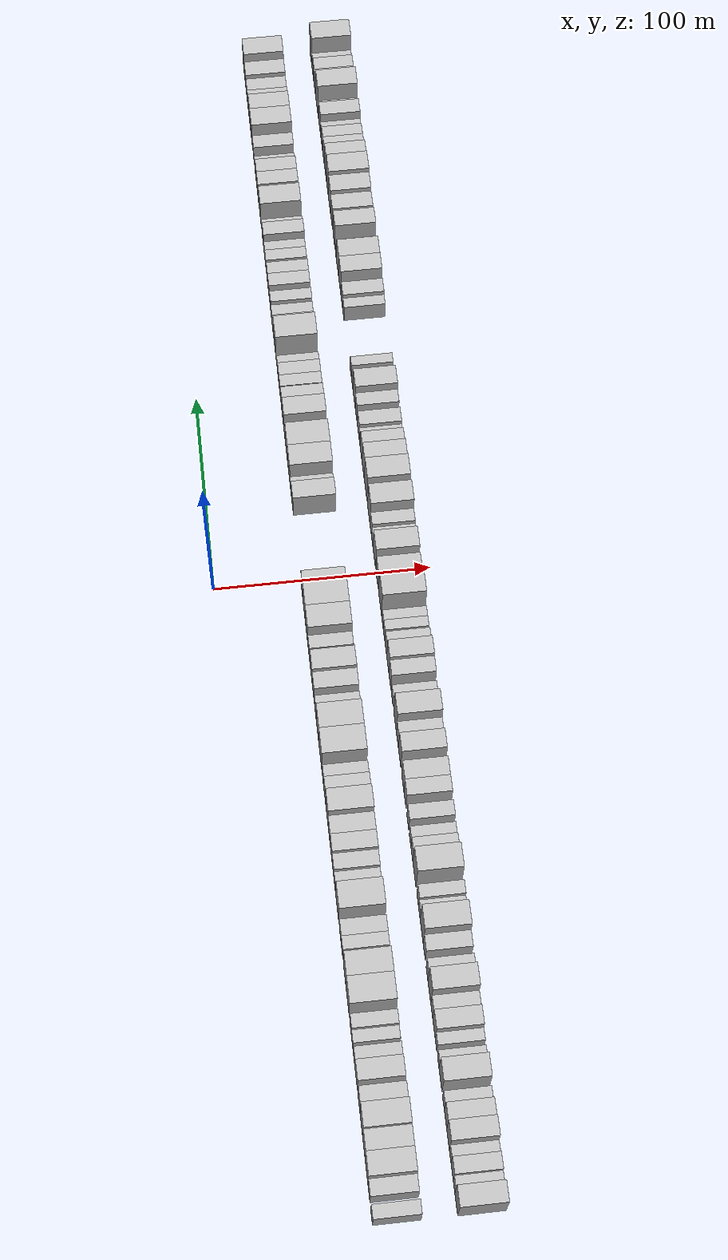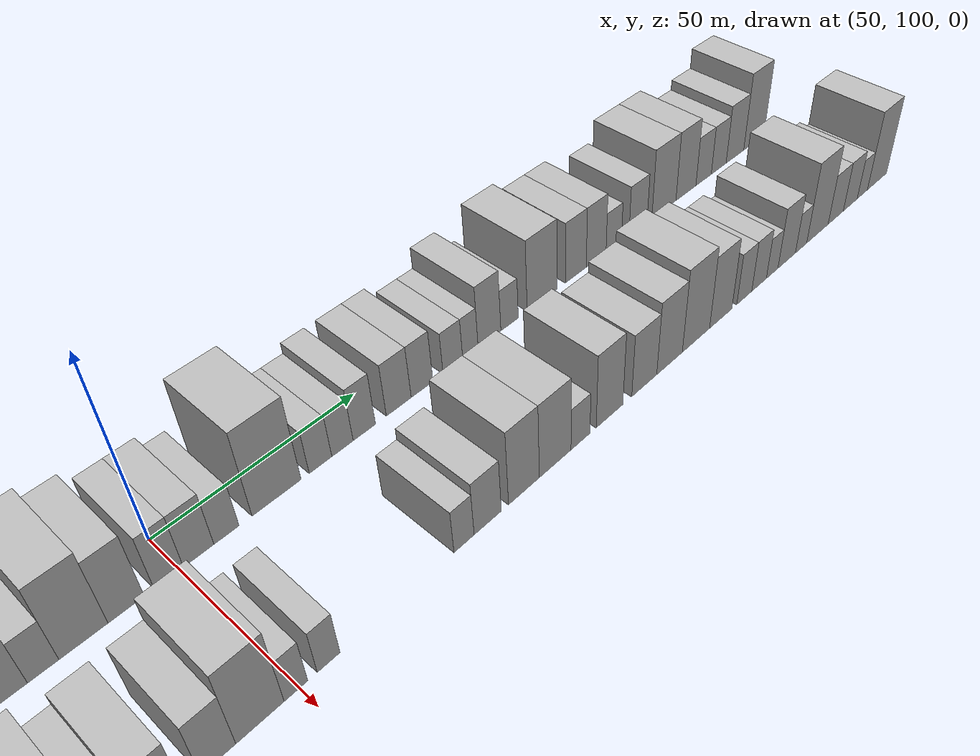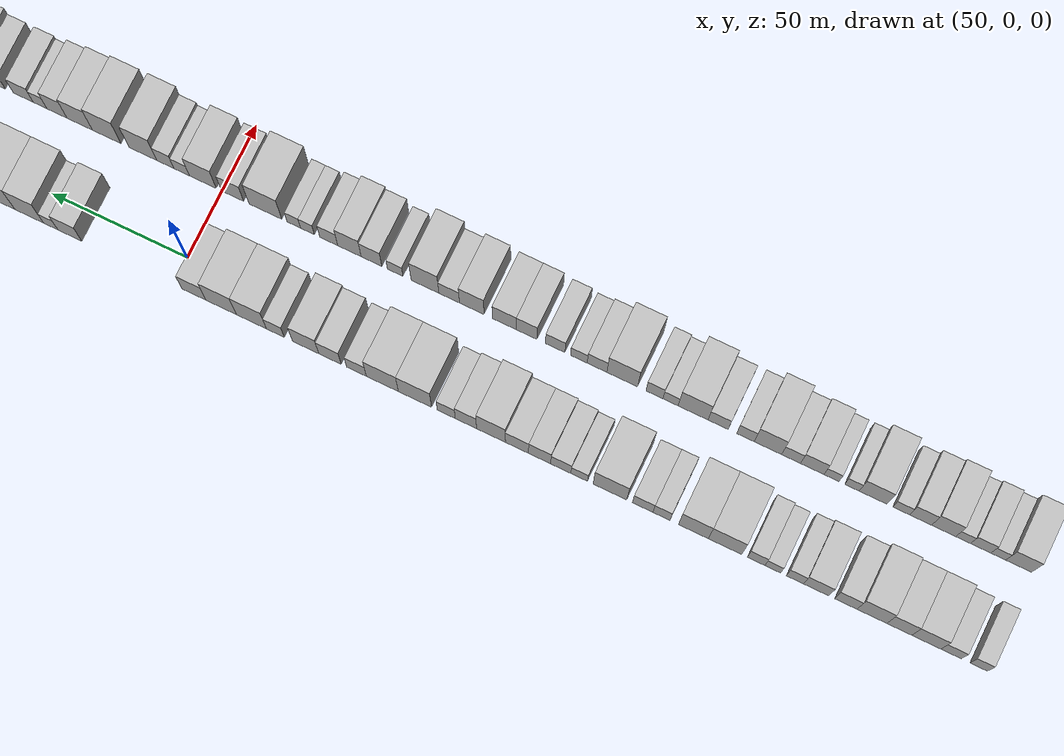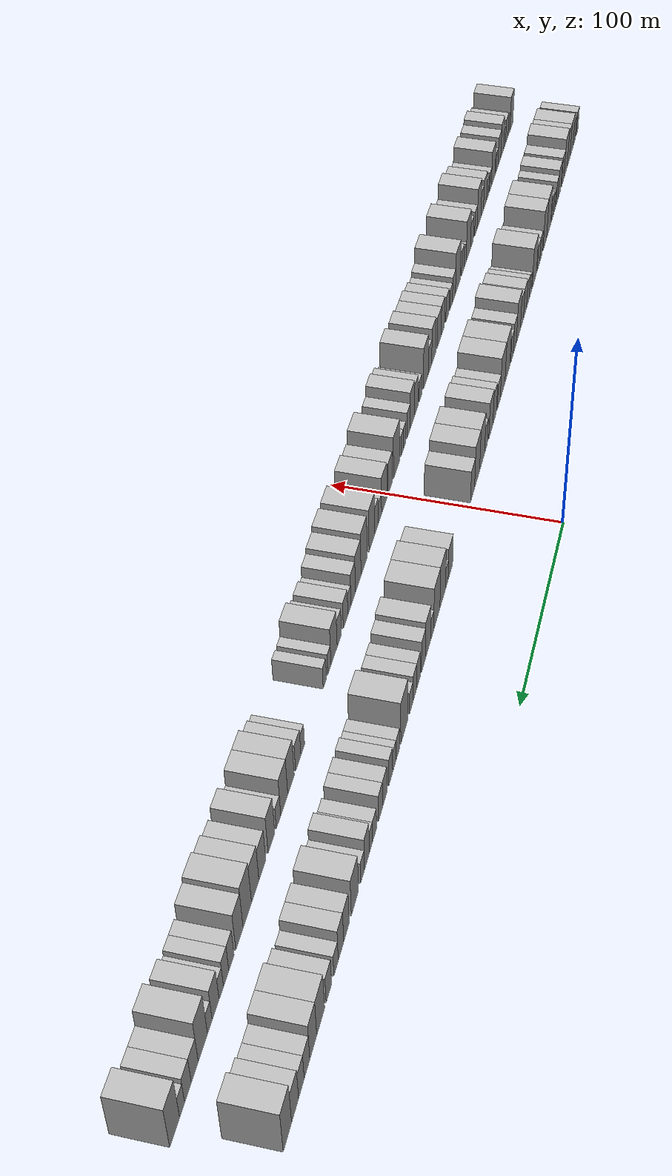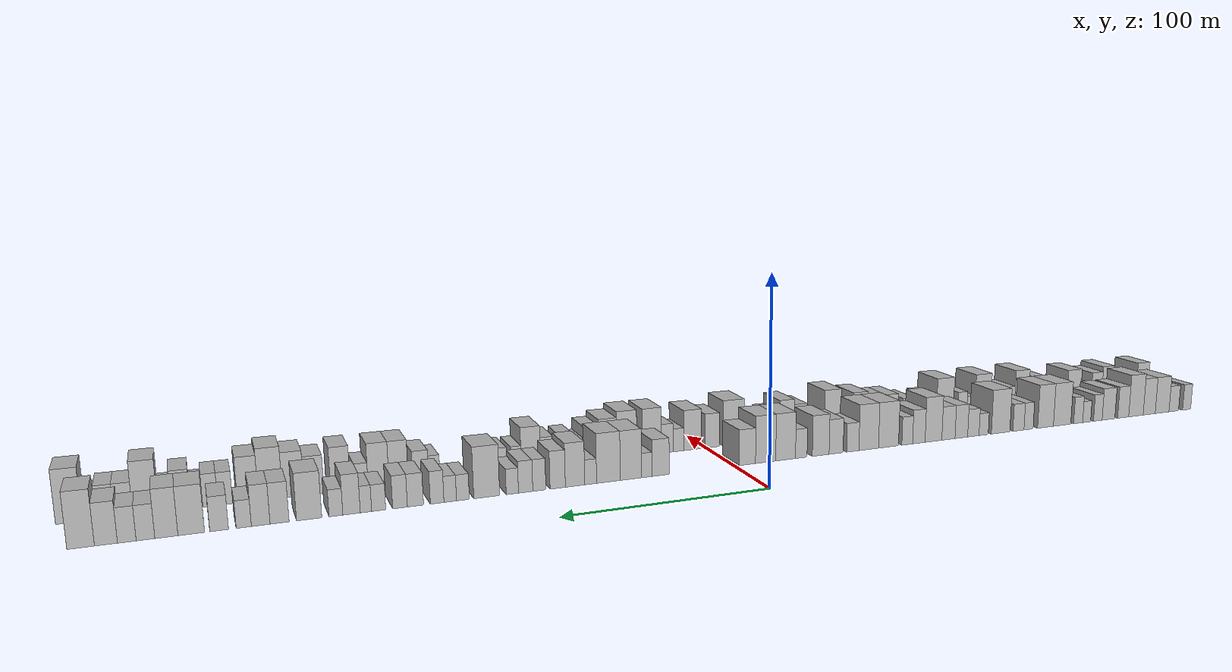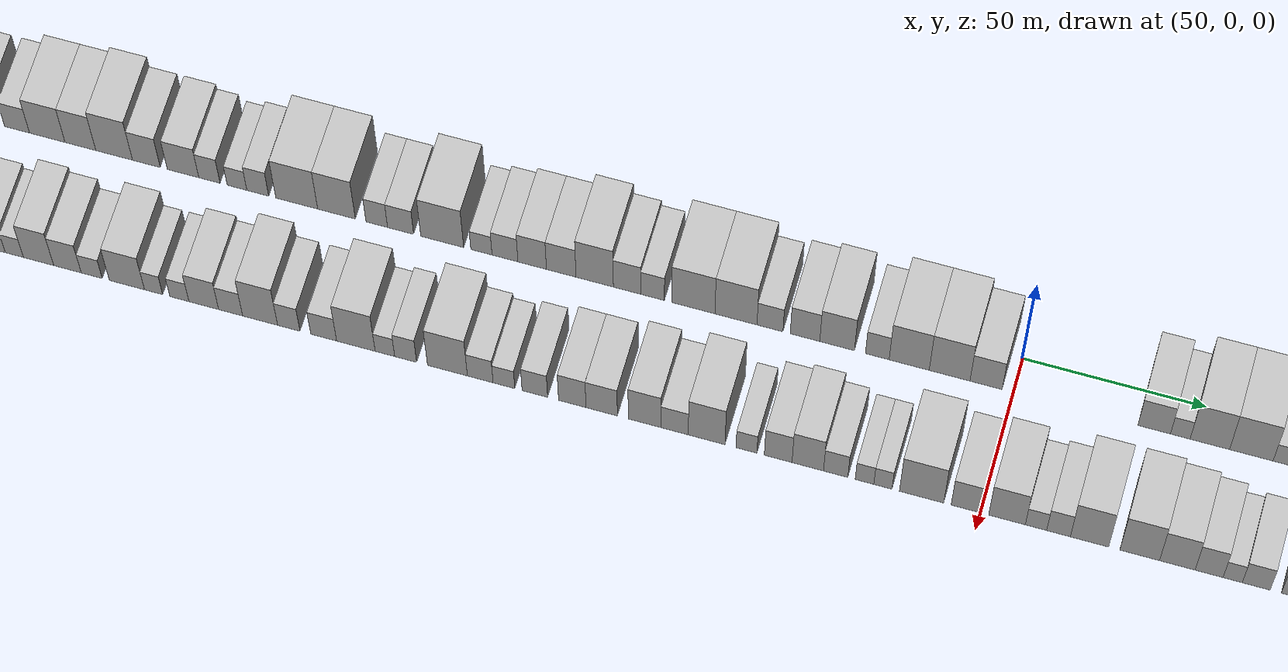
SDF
<sdf version="1.6">
 <world name="default">
  <scene>
   <sky><clouds><speed>12</speed></clouds></sky>
   <ambient>0.4 0.4 0.4 1</ambient>
   <background>0.7 0.7 0.7 1</background>
   <shadows>1</shadows>
  </scene>
  <gravity>0 0 -9.8066</gravity>
  <magnetic_field>6e-06 2.3e-05 -4.2e-05</magnetic_field>
  <physics default="0" name="default_physics" type="ode">
   <ode>
    <solver>
     <type>quick</type>
     <iters>10</iters>
     <sor>1.0</sor>
     <use_dynamic_moi_rescaling>0</use_dynamic_moi_rescaling>
    </solver>
    <constraints>
     <cfm>0</cfm>
     <erp>0.2</erp>
     <contact_max_correcting_vel>100</contact_max_correcting_vel>
     <contact_surface_layer>0.001</contact_surface_layer>
    </constraints>
   </ode>
   <max_step_size>0.004</max_step_size>
   <real_time_factor>1</real_time_factor>
   <real_time_update_rate>250</real_time_update_rate>
  </physics>
  <light name="sun" type="directional">
   <pose>0 0 10 0 0 0</pose>
   <diffuse>0.8 0.8 0.8 1</diffuse>
   <specular>0.2 0.2 0.2 1</specular>
   <attenuation>
    <range>1000</range>
    <constant>0.9</constant>
    <linear>0.01</linear>
    <quadratic>0.001</quadratic>
   </attenuation>
   <direction>-0.5 0.1 -0.9</direction>
  </light>
  <model name="building_1">
   <static>1</static>
   <pose>50.0000 -286.9867 0 0.000000 0.000000 0.000000</pose>
   <link name="link">
    <pose>0 0 7.50 0 0 0</pose>
    <collision name="collision"><geometry><box><size>20.0000 6.0265 15.0000</size></box></geometry></collision>
    <visual name="visual">
     <cast_shadows>0</cast_shadows>
     <geometry><box><size>20.0000 6.0265 15.0000</size></box></geometry>
     <material>
      <script>
       <uri>model://HANNAS_wall/materials/scripts</uri>
       <uri>model://HANNAS_wall/materials/textures</uri>
       <name>vrc/HANNAS_wall</name>
      </script>
     </material>
    </visual>
   </link>
  </model>
  <model name="building_2">
   <static>1</static>
   <pose>50.0000 -277.4261 0 0.000000 0.000000 0.000000</pose>
   <link name="link">
    <pose>0 0 7.50 0 0 0</pose>
    <collision name="collision"><geometry><box><size>20.0000 7.0948 15.0000</size></box></geometry></collision>
    <visual name="visual">
     <cast_shadows>0</cast_shadows>
     <geometry><box><size>20.0000 7.0948 15.0000</size></box></geometry>
     <material>
      <script>
       <uri>model://HANNAS_wall/materials/scripts</uri>
       <uri>model://HANNAS_wall/materials/textures</uri>
       <name>vrc/HANNAS_wall</name>
      </script>
     </material>
    </visual>
   </link>
  </model>
  <model name="building_3">
   <static>1</static>
   <pose>50.0000 -268.8254 0 0.000000 0.000000 0.000000</pose>
   <link name="link">
    <pose>0 0 10.50 0 0 0</pose>
    <collision name="collision"><geometry><box><size>20.0000 10.1066 21.0000</size></box></geometry></collision>
    <visual name="visual">
     <cast_shadows>0</cast_shadows>
     <geometry><box><size>20.0000 10.1066 21.0000</size></box></geometry>
     <material>
      <script>
       <uri>model://HANNAS_wall/materials/scripts</uri>
       <uri>model://HANNAS_wall/materials/textures</uri>
       <name>vrc/HANNAS_wall</name>
      </script>
     </material>
    </visual>
   </link>
  </model>
  <model name="building_4">
   <static>1</static>
   <pose>50.0000 -259.3988 0 0.000000 0.000000 0.000000</pose>
   <link name="link">
    <pose>0 0 10.50 0 0 0</pose>
    <collision name="collision"><geometry><box><size>20.0000 8.7465 21.0000</size></box></geometry></collision>
    <visual name="visual">
     <cast_shadows>0</cast_shadows>
     <geometry><box><size>20.0000 8.7465 21.0000</size></box></geometry>
     <material>
      <script>
       <uri>model://HANNAS_wall/materials/scripts</uri>
       <uri>model://HANNAS_wall/materials/textures</uri>
       <name>vrc/HANNAS_wall</name>
      </script>
     </material>
    </visual>
   </link>
  </model>
  <model name="building_5">
   <static>1</static>
   <pose>50.0000 -249.8142 0 0.000000 0.000000 0.000000</pose>
   <link name="link">
    <pose>0 0 12.00 0 0 0</pose>
    <collision name="collision"><geometry><box><size>20.0000 10.4228 24.0000</size></box></geometry></collision>
    <visual name="visual">
     <cast_shadows>0</cast_shadows>
     <geometry><box><size>20.0000 10.4228 24.0000</size></box></geometry>
     <material>
      <script>
       <uri>model://HANNAS_wall/materials/scripts</uri>
       <uri>model://HANNAS_wall/materials/textures</uri>
       <name>vrc/HANNAS_wall</name>
      </script>
     </material>
    </visual>
   </link>
  </model>
  <model name="building_6">
   <static>1</static>
   <pose>50.0000 -240.6786 0 0.000000 0.000000 0.000000</pose>
   <link name="link">
    <pose>0 0 9.00 0 0 0</pose>
    <collision name="collision"><geometry><box><size>20.0000 7.8482 18.0000</size></box></geometry></collision>
    <visual name="visual">
     <cast_shadows>0</cast_shadows>
     <geometry><box><size>20.0000 7.8482 18.0000</size></box></geometry>
     <material>
      <script>
       <uri>model://HANNAS_wall/materials/scripts</uri>
       <uri>model://HANNAS_wall/materials/textures</uri>
       <name>vrc/HANNAS_wall</name>
      </script>
     </material>
    </visual>
   </link>
  </model>
  <model name="building_7">
   <static>1</static>
   <pose>50.0000 -230.2864 0 0.000000 0.000000 0.000000</pose>
   <link name="link">
    <pose>0 0 9.00 0 0 0</pose>
    <collision name="collision"><geometry><box><size>20.0000 8.9361 18.0000</size></box></geometry></collision>
    <visual name="visual">
     <cast_shadows>0</cast_shadows>
     <geometry><box><size>20.0000 8.9361 18.0000</size></box></geometry>
     <material>
      <script>
       <uri>model://HANNAS_wall/materials/scripts</uri>
       <uri>model://HANNAS_wall/materials/textures</uri>
       <name>vrc/HANNAS_wall</name>
      </script>
     </material>
    </visual>
   </link>
  </model>
  <model name="building_8">
   <static>1</static>
   <pose>50.0000 -222.8066 0 0.000000 0.000000 0.000000</pose>
   <link name="link">
    <pose>0 0 7.50 0 0 0</pose>
    <collision name="collision"><geometry><box><size>20.0000 6.0235 15.0000</size></box></geometry></collision>
    <visual name="visual">
     <cast_shadows>0</cast_shadows>
     <geometry><box><size>20.0000 6.0235 15.0000</size></box></geometry>
     <material>
      <script>
       <uri>model://HANNAS_wall/materials/scripts</uri>
       <uri>model://HANNAS_wall/materials/textures</uri>
       <name>vrc/HANNAS_wall</name>
      </script>
     </material>
    </visual>
   </link>
  </model>
  <model name="building_9">
   <static>1</static>
   <pose>50.0000 -215.0221 0 0.000000 0.000000 0.000000</pose>
   <link name="link">
    <pose>0 0 6.00 0 0 0</pose>
    <collision name="collision"><geometry><box><size>20.0000 5.5455 12.0000</size></box></geometry></collision>
    <visual name="visual">
     <cast_shadows>0</cast_shadows>
     <geometry><box><size>20.0000 5.5455 12.0000</size></box></geometry>
     <material>
      <script>
       <uri>model://HANNAS_wall/materials/scripts</uri>
       <uri>model://HANNAS_wall/materials/textures</uri>
       <name>vrc/HANNAS_wall</name>
      </script>
     </material>
    </visual>
   </link>
  </model>
  <model name="building_10">
   <static>1</static>
   <pose>50.0000 -209.1622 0 0.000000 0.000000 0.000000</pose>
   <link name="link">
    <pose>0 0 7.50 0 0 0</pose>
    <collision name="collision"><geometry><box><size>20.0000 6.1743 15.0000</size></box></geometry></collision>
    <visual name="visual">
     <cast_shadows>0</cast_shadows>
     <geometry><box><size>20.0000 6.1743 15.0000</size></box></geometry>
     <material>
      <script>
       <uri>model://HANNAS_wall/materials/scripts</uri>
       <uri>model://HANNAS_wall/materials/textures</uri>
       <name>vrc/HANNAS_wall</name>
      </script>
     </material>
    </visual>
   </link>
  </model>
  <model name="building_11">
   <static>1</static>
   <pose>50.0000 -198.1938 0 0.000000 0.000000 0.000000</pose>
   <link name="link">
    <pose>0 0 12.00 0 0 0</pose>
    <collision name="collision"><geometry><box><size>20.0000 11.7625 24.0000</size></box></geometry></collision>
    <visual name="visual">
     <cast_shadows>0</cast_shadows>
     <geometry><box><size>20.0000 11.7625 24.0000</size></box></geometry>
     <material>
      <script>
       <uri>model://HANNAS_wall/materials/scripts</uri>
       <uri>model://HANNAS_wall/materials/textures</uri>
       <name>vrc/HANNAS_wall</name>
      </script>
     </material>
    </visual>
   </link>
  </model>
  <model name="building_12">
   <static>1</static>
   <pose>50.0000 -187.0191 0 0.000000 0.000000 0.000000</pose>
   <link name="link">
    <pose>0 0 12.00 0 0 0</pose>
    <collision name="collision"><geometry><box><size>20.0000 10.5870 24.0000</size></box></geometry></collision>
    <visual name="visual">
     <cast_shadows>0</cast_shadows>
     <geometry><box><size>20.0000 10.5870 24.0000</size></box></geometry>
     <material>
      <script>
       <uri>model://HANNAS_wall/materials/scripts</uri>
       <uri>model://HANNAS_wall/materials/textures</uri>
       <name>vrc/HANNAS_wall</name>
      </script>
     </material>
    </visual>
   </link>
  </model>
  <model name="building_13">
   <static>1</static>
   <pose>50.0000 -175.7036 0 0.000000 0.000000 0.000000</pose>
   <link name="link">
    <pose>0 0 7.50 0 0 0</pose>
    <collision name="collision"><geometry><box><size>20.0000 6.0440 15.0000</size></box></geometry></collision>
    <visual name="visual">
     <cast_shadows>0</cast_shadows>
     <geometry><box><size>20.0000 6.0440 15.0000</size></box></geometry>
     <material>
      <script>
       <uri>model://HANNAS_wall/materials/scripts</uri>
       <uri>model://HANNAS_wall/materials/textures</uri>
       <name>vrc/HANNAS_wall</name>
      </script>
     </material>
    </visual>
   </link>
  </model>
  <model name="building_14">
   <static>1</static>
   <pose>50.0000 -169.0348 0 0.000000 0.000000 0.000000</pose>
   <link name="link">
    <pose>0 0 7.50 0 0 0</pose>
    <collision name="collision"><geometry><box><size>20.0000 7.2937 15.0000</size></box></geometry></collision>
    <visual name="visual">
     <cast_shadows>0</cast_shadows>
     <geometry><box><size>20.0000 7.2937 15.0000</size></box></geometry>
     <material>
      <script>
       <uri>model://HANNAS_wall/materials/scripts</uri>
       <uri>model://HANNAS_wall/materials/textures</uri>
       <name>vrc/HANNAS_wall</name>
      </script>
     </material>
    </visual>
   </link>
  </model>
  <model name="building_15">
   <static>1</static>
   <pose>50.0000 -157.3991 0 0.000000 0.000000 0.000000</pose>
   <link name="link">
    <pose>0 0 12.00 0 0 0</pose>
    <collision name="collision"><geometry><box><size>20.0000 11.9776 24.0000</size></box></geometry></collision>
    <visual name="visual">
     <cast_shadows>0</cast_shadows>
     <geometry><box><size>20.0000 11.9776 24.0000</size></box></geometry>
     <material>
      <script>
       <uri>model://HANNAS_wall/materials/scripts</uri>
       <uri>model://HANNAS_wall/materials/textures</uri>
       <name>vrc/HANNAS_wall</name>
      </script>
     </material>
    </visual>
   </link>
  </model>
  <model name="building_16">
   <static>1</static>
   <pose>50.0000 -146.4578 0 0.000000 0.000000 0.000000</pose>
   <link name="link">
    <pose>0 0 6.00 0 0 0</pose>
    <collision name="collision"><geometry><box><size>20.0000 5.9051 12.0000</size></box></geometry></collision>
    <visual name="visual">
     <cast_shadows>0</cast_shadows>
     <geometry><box><size>20.0000 5.9051 12.0000</size></box></geometry>
     <material>
      <script>
       <uri>model://HANNAS_wall/materials/scripts</uri>
       <uri>model://HANNAS_wall/materials/textures</uri>
       <name>vrc/HANNAS_wall</name>
      </script>
     </material>
    </visual>
   </link>
  </model>
  <model name="building_17">
   <static>1</static>
   <pose>50.0000 -139.8941 0 0.000000 0.000000 0.000000</pose>
   <link name="link">
    <pose>0 0 7.50 0 0 0</pose>
    <collision name="collision"><geometry><box><size>20.0000 7.2222 15.0000</size></box></geometry></collision>
    <visual name="visual">
     <cast_shadows>0</cast_shadows>
     <geometry><box><size>20.0000 7.2222 15.0000</size></box></geometry>
     <material>
      <script>
       <uri>model://HANNAS_wall/materials/scripts</uri>
       <uri>model://HANNAS_wall/materials/textures</uri>
       <name>vrc/HANNAS_wall</name>
      </script>
     </material>
    </visual>
   </link>
  </model>
  <model name="building_18">
   <static>1</static>
   <pose>50.0000 -132.3141 0 0.000000 0.000000 0.000000</pose>
   <link name="link">
    <pose>0 0 9.00 0 0 0</pose>
    <collision name="collision"><geometry><box><size>20.0000 7.9379 18.0000</size></box></geometry></collision>
    <visual name="visual">
     <cast_shadows>0</cast_shadows>
     <geometry><box><size>20.0000 7.9379 18.0000</size></box></geometry>
     <material>
      <script>
       <uri>model://HANNAS_wall/materials/scripts</uri>
       <uri>model://HANNAS_wall/materials/textures</uri>
       <name>vrc/HANNAS_wall</name>
      </script>
     </material>
    </visual>
   </link>
  </model>
  <model name="building_19">
   <static>1</static>
   <pose>50.0000 -124.2348 0 0.000000 0.000000 0.000000</pose>
   <link name="link">
    <pose>0 0 9.00 0 0 0</pose>
    <collision name="collision"><geometry><box><size>20.0000 8.2207 18.0000</size></box></geometry></collision>
    <visual name="visual">
     <cast_shadows>0</cast_shadows>
     <geometry><box><size>20.0000 8.2207 18.0000</size></box></geometry>
     <material>
      <script>
       <uri>model://HANNAS_wall/materials/scripts</uri>
       <uri>model://HANNAS_wall/materials/textures</uri>
       <name>vrc/HANNAS_wall</name>
      </script>
     </material>
    </visual>
   </link>
  </model>
  <model name="building_20">
   <static>1</static>
   <pose>50.0000 -114.9453 0 0.000000 0.000000 0.000000</pose>
   <link name="link">
    <pose>0 0 12.00 0 0 0</pose>
    <collision name="collision"><geometry><box><size>20.0000 10.3582 24.0000</size></box></geometry></collision>
    <visual name="visual">
     <cast_shadows>0</cast_shadows>
     <geometry><box><size>20.0000 10.3582 24.0000</size></box></geometry>
     <material>
      <script>
       <uri>model://HANNAS_wall/materials/scripts</uri>
       <uri>model://HANNAS_wall/materials/textures</uri>
       <name>vrc/HANNAS_wall</name>
      </script>
     </material>
    </visual>
   </link>
  </model>
  <model name="building_21">
   <static>1</static>
   <pose>50.0000 -105.9555 0 0.000000 0.000000 0.000000</pose>
   <link name="link">
    <pose>0 0 9.00 0 0 0</pose>
    <collision name="collision"><geometry><box><size>20.0000 7.6214 18.0000</size></box></geometry></collision>
    <visual name="visual">
     <cast_shadows>0</cast_shadows>
     <geometry><box><size>20.0000 7.6214 18.0000</size></box></geometry>
     <material>
      <script>
       <uri>model://HANNAS_wall/materials/scripts</uri>
       <uri>model://HANNAS_wall/materials/textures</uri>
       <name>vrc/HANNAS_wall</name>
      </script>
     </material>
    </visual>
   </link>
  </model>
  <model name="building_22">
   <static>1</static>
   <pose>50.0000 -98.8913 0 0.000000 0.000000 0.000000</pose>
   <link name="link">
    <pose>0 0 7.50 0 0 0</pose>
    <collision name="collision"><geometry><box><size>20.0000 6.5070 15.0000</size></box></geometry></collision>
    <visual name="visual">
     <cast_shadows>0</cast_shadows>
     <geometry><box><size>20.0000 6.5070 15.0000</size></box></geometry>
     <material>
      <script>
       <uri>model://HANNAS_wall/materials/scripts</uri>
       <uri>model://HANNAS_wall/materials/textures</uri>
       <name>vrc/HANNAS_wall</name>
      </script>
     </material>
    </visual>
   </link>
  </model>
  <model name="building_23">
   <static>1</static>
   <pose>50.0000 -87.6615 0 0.000000 0.000000 0.000000</pose>
   <link name="link">
    <pose>0 0 12.00 0 0 0</pose>
    <collision name="collision"><geometry><box><size>20.0000 11.9526 24.0000</size></box></geometry></collision>
    <visual name="visual">
     <cast_shadows>0</cast_shadows>
     <geometry><box><size>20.0000 11.9526 24.0000</size></box></geometry>
     <material>
      <script>
       <uri>model://HANNAS_wall/materials/scripts</uri>
       <uri>model://HANNAS_wall/materials/textures</uri>
       <name>vrc/HANNAS_wall</name>
      </script>
     </material>
    </visual>
   </link>
  </model>
  <model name="building_24">
   <static>1</static>
   <pose>50.0000 -75.9016 0 0.000000 0.000000 0.000000</pose>
   <link name="link">
    <pose>0 0 12.00 0 0 0</pose>
    <collision name="collision"><geometry><box><size>20.0000 11.5673 24.0000</size></box></geometry></collision>
    <visual name="visual">
     <cast_shadows>0</cast_shadows>
     <geometry><box><size>20.0000 11.5673 24.0000</size></box></geometry>
     <material>
      <script>
       <uri>model://HANNAS_wall/materials/scripts</uri>
       <uri>model://HANNAS_wall/materials/textures</uri>
       <name>vrc/HANNAS_wall</name>
      </script>
     </material>
    </visual>
   </link>
  </model>
  <model name="building_25">
   <static>1</static>
   <pose>50.0000 -66.5488 0 0.000000 0.000000 0.000000</pose>
   <link name="link">
    <pose>0 0 7.50 0 0 0</pose>
    <collision name="collision"><geometry><box><size>20.0000 7.1383 15.0000</size></box></geometry></collision>
    <visual name="visual">
     <cast_shadows>0</cast_shadows>
     <geometry><box><size>20.0000 7.1383 15.0000</size></box></geometry>
     <material>
      <script>
       <uri>model://HANNAS_wall/materials/scripts</uri>
       <uri>model://HANNAS_wall/materials/textures</uri>
       <name>vrc/HANNAS_wall</name>
      </script>
     </material>
    </visual>
   </link>
  </model>
  <model name="building_26">
   <static>1</static>
   <pose>50.0000 -56.9321 0 0.000000 0.000000 0.000000</pose>
   <link name="link">
    <pose>0 0 9.00 0 0 0</pose>
    <collision name="collision"><geometry><box><size>20.0000 8.0951 18.0000</size></box></geometry></collision>
    <visual name="visual">
     <cast_shadows>0</cast_shadows>
     <geometry><box><size>20.0000 8.0951 18.0000</size></box></geometry>
     <material>
      <script>
       <uri>model://HANNAS_wall/materials/scripts</uri>
       <uri>model://HANNAS_wall/materials/textures</uri>
       <name>vrc/HANNAS_wall</name>
      </script>
     </material>
    </visual>
   </link>
  </model>
  <model name="building_27">
   <static>1</static>
   <pose>50.0000 -48.1220 0 0.000000 0.000000 0.000000</pose>
   <link name="link">
    <pose>0 0 10.50 0 0 0</pose>
    <collision name="collision"><geometry><box><size>20.0000 9.5251 21.0000</size></box></geometry></collision>
    <visual name="visual">
     <cast_shadows>0</cast_shadows>
     <geometry><box><size>20.0000 9.5251 21.0000</size></box></geometry>
     <material>
      <script>
       <uri>model://HANNAS_wall/materials/scripts</uri>
       <uri>model://HANNAS_wall/materials/textures</uri>
       <name>vrc/HANNAS_wall</name>
      </script>
     </material>
    </visual>
   </link>
  </model>
  <model name="building_28">
   <static>1</static>
   <pose>50.0000 -37.1234 0 0.000000 0.000000 0.000000</pose>
   <link name="link">
    <pose>0 0 7.50 0 0 0</pose>
    <collision name="collision"><geometry><box><size>20.0000 6.4721 15.0000</size></box></geometry></collision>
    <visual name="visual">
     <cast_shadows>0</cast_shadows>
     <geometry><box><size>20.0000 6.4721 15.0000</size></box></geometry>
     <material>
      <script>
       <uri>model://HANNAS_wall/materials/scripts</uri>
       <uri>model://HANNAS_wall/materials/textures</uri>
       <name>vrc/HANNAS_wall</name>
      </script>
     </material>
    </visual>
   </link>
  </model>
  <model name="building_29">
   <static>1</static>
   <pose>50.0000 -28.4028 0 0.000000 0.000000 0.000000</pose>
   <link name="link">
    <pose>0 0 12.00 0 0 0</pose>
    <collision name="collision"><geometry><box><size>20.0000 10.9692 24.0000</size></box></geometry></collision>
    <visual name="visual">
     <cast_shadows>0</cast_shadows>
     <geometry><box><size>20.0000 10.9692 24.0000</size></box></geometry>
     <material>
      <script>
       <uri>model://HANNAS_wall/materials/scripts</uri>
       <uri>model://HANNAS_wall/materials/textures</uri>
       <name>vrc/HANNAS_wall</name>
      </script>
     </material>
    </visual>
   </link>
  </model>
  <model name="building_30">
   <static>1</static>
   <pose>50.0000 -17.3656 0 0.000000 0.000000 0.000000</pose>
   <link name="link">
    <pose>0 0 12.00 0 0 0</pose>
    <collision name="collision"><geometry><box><size>20.0000 11.1053 24.0000</size></box></geometry></collision>
    <visual name="visual">
     <cast_shadows>0</cast_shadows>
     <geometry><box><size>20.0000 11.1053 24.0000</size></box></geometry>
     <material>
      <script>
       <uri>model://HANNAS_wall/materials/scripts</uri>
       <uri>model://HANNAS_wall/materials/textures</uri>
       <name>vrc/HANNAS_wall</name>
      </script>
     </material>
    </visual>
   </link>
  </model>
  <model name="building_31">
   <static>1</static>
   <pose>50.0000 -7.4308 0 0.000000 0.000000 0.000000</pose>
   <link name="link">
    <pose>0 0 9.00 0 0 0</pose>
    <collision name="collision"><geometry><box><size>20.0000 8.7644 18.0000</size></box></geometry></collision>
    <visual name="visual">
     <cast_shadows>0</cast_shadows>
     <geometry><box><size>20.0000 8.7644 18.0000</size></box></geometry>
     <material>
      <script>
       <uri>model://HANNAS_wall/materials/scripts</uri>
       <uri>model://HANNAS_wall/materials/textures</uri>
       <name>vrc/HANNAS_wall</name>
      </script>
     </material>
    </visual>
   </link>
  </model>
  <model name="building_32">
   <static>1</static>
   <pose>50.0000 38.1596 0 0.000000 0.000000 0.000000</pose>
   <link name="link">
    <pose>0 0 9.00 0 0 0</pose>
    <collision name="collision"><geometry><box><size>20.0000 8.8054 18.0000</size></box></geometry></collision>
    <visual name="visual">
     <cast_shadows>0</cast_shadows>
     <geometry><box><size>20.0000 8.8054 18.0000</size></box></geometry>
     <material>
      <script>
       <uri>model://HANNAS_wall/materials/scripts</uri>
       <uri>model://HANNAS_wall/materials/textures</uri>
       <name>vrc/HANNAS_wall</name>
      </script>
     </material>
    </visual>
   </link>
  </model>
  <model name="building_33">
   <static>1</static>
   <pose>50.0000 45.2010 0 0.000000 0.000000 0.000000</pose>
   <link name="link">
    <pose>0 0 6.00 0 0 0</pose>
    <collision name="collision"><geometry><box><size>20.0000 5.2773 12.0000</size></box></geometry></collision>
    <visual name="visual">
     <cast_shadows>0</cast_shadows>
     <geometry><box><size>20.0000 5.2773 12.0000</size></box></geometry>
     <material>
      <script>
       <uri>model://HANNAS_wall/materials/scripts</uri>
       <uri>model://HANNAS_wall/materials/textures</uri>
       <name>vrc/HANNAS_wall</name>
      </script>
     </material>
    </visual>
   </link>
  </model>
  <model name="building_34">
   <static>1</static>
   <pose>50.0000 53.1479 0 0.000000 0.000000 0.000000</pose>
   <link name="link">
    <pose>0 0 12.00 0 0 0</pose>
    <collision name="collision"><geometry><box><size>20.0000 10.6165 24.0000</size></box></geometry></collision>
    <visual name="visual">
     <cast_shadows>0</cast_shadows>
     <geometry><box><size>20.0000 10.6165 24.0000</size></box></geometry>
     <material>
      <script>
       <uri>model://HANNAS_wall/materials/scripts</uri>
       <uri>model://HANNAS_wall/materials/textures</uri>
       <name>vrc/HANNAS_wall</name>
      </script>
     </material>
    </visual>
   </link>
  </model>
  <model name="building_35">
   <static>1</static>
   <pose>50.0000 64.3146 0 0.000000 0.000000 0.000000</pose>
   <link name="link">
    <pose>0 0 12.00 0 0 0</pose>
    <collision name="collision"><geometry><box><size>20.0000 11.7168 24.0000</size></box></geometry></collision>
    <visual name="visual">
     <cast_shadows>0</cast_shadows>
     <geometry><box><size>20.0000 11.7168 24.0000</size></box></geometry>
     <material>
      <script>
       <uri>model://HANNAS_wall/materials/scripts</uri>
       <uri>model://HANNAS_wall/materials/textures</uri>
       <name>vrc/HANNAS_wall</name>
      </script>
     </material>
    </visual>
   </link>
  </model>
  <model name="building_36">
   <static>1</static>
   <pose>50.0000 73.0456 0 0.000000 0.000000 0.000000</pose>
   <link name="link">
    <pose>0 0 6.00 0 0 0</pose>
    <collision name="collision"><geometry><box><size>20.0000 5.7453 12.0000</size></box></geometry></collision>
    <visual name="visual">
     <cast_shadows>0</cast_shadows>
     <geometry><box><size>20.0000 5.7453 12.0000</size></box></geometry>
     <material>
      <script>
       <uri>model://HANNAS_wall/materials/scripts</uri>
       <uri>model://HANNAS_wall/materials/textures</uri>
       <name>vrc/HANNAS_wall</name>
      </script>
     </material>
    </visual>
   </link>
  </model>
  <model name="building_37">
   <static>1</static>
   <pose>50.0000 80.6158 0 0.000000 0.000000 0.000000</pose>
   <link name="link">
    <pose>0 0 10.50 0 0 0</pose>
    <collision name="collision"><geometry><box><size>20.0000 9.3951 21.0000</size></box></geometry></collision>
    <visual name="visual">
     <cast_shadows>0</cast_shadows>
     <geometry><box><size>20.0000 9.3951 21.0000</size></box></geometry>
     <material>
      <script>
       <uri>model://HANNAS_wall/materials/scripts</uri>
       <uri>model://HANNAS_wall/materials/textures</uri>
       <name>vrc/HANNAS_wall</name>
      </script>
     </material>
    </visual>
   </link>
  </model>
  <model name="building_38">
   <static>1</static>
   <pose>50.0000 88.9659 0 0.000000 0.000000 0.000000</pose>
   <link name="link">
    <pose>0 0 9.00 0 0 0</pose>
    <collision name="collision"><geometry><box><size>20.0000 7.3051 18.0000</size></box></geometry></collision>
    <visual name="visual">
     <cast_shadows>0</cast_shadows>
     <geometry><box><size>20.0000 7.3051 18.0000</size></box></geometry>
     <material>
      <script>
       <uri>model://HANNAS_wall/materials/scripts</uri>
       <uri>model://HANNAS_wall/materials/textures</uri>
       <name>vrc/HANNAS_wall</name>
      </script>
     </material>
    </visual>
   </link>
  </model>
  <model name="building_39">
   <static>1</static>
   <pose>50.0000 97.7068 0 0.000000 0.000000 0.000000</pose>
   <link name="link">
    <pose>0 0 7.50 0 0 0</pose>
    <collision name="collision"><geometry><box><size>20.0000 6.1767 15.0000</size></box></geometry></collision>
    <visual name="visual">
     <cast_shadows>0</cast_shadows>
     <geometry><box><size>20.0000 6.1767 15.0000</size></box></geometry>
     <material>
      <script>
       <uri>model://HANNAS_wall/materials/scripts</uri>
       <uri>model://HANNAS_wall/materials/textures</uri>
       <name>vrc/HANNAS_wall</name>
      </script>
     </material>
    </visual>
   </link>
  </model>
  <model name="building_40">
   <static>1</static>
   <pose>50.0000 104.1359 0 0.000000 0.000000 0.000000</pose>
   <link name="link">
    <pose>0 0 7.50 0 0 0</pose>
    <collision name="collision"><geometry><box><size>20.0000 6.6816 15.0000</size></box></geometry></collision>
    <visual name="visual">
     <cast_shadows>0</cast_shadows>
     <geometry><box><size>20.0000 6.6816 15.0000</size></box></geometry>
     <material>
      <script>
       <uri>model://HANNAS_wall/materials/scripts</uri>
       <uri>model://HANNAS_wall/materials/textures</uri>
       <name>vrc/HANNAS_wall</name>
      </script>
     </material>
    </visual>
   </link>
  </model>
  <model name="building_41">
   <static>1</static>
   <pose>50.0000 110.3209 0 0.000000 0.000000 0.000000</pose>
   <link name="link">
    <pose>0 0 6.00 0 0 0</pose>
    <collision name="collision"><geometry><box><size>20.0000 5.6883 12.0000</size></box></geometry></collision>
    <visual name="visual">
     <cast_shadows>0</cast_shadows>
     <geometry><box><size>20.0000 5.6883 12.0000</size></box></geometry>
     <material>
      <script>
       <uri>model://HANNAS_wall/materials/scripts</uri>
       <uri>model://HANNAS_wall/materials/textures</uri>
       <name>vrc/HANNAS_wall</name>
      </script>
     </material>
    </visual>
   </link>
  </model>
  <model name="building_42">
   <static>1</static>
   <pose>50.0000 122.0882 0 0.000000 0.000000 0.000000</pose>
   <link name="link">
    <pose>0 0 12.00 0 0 0</pose>
    <collision name="collision"><geometry><box><size>20.0000 11.8464 24.0000</size></box></geometry></collision>
    <visual name="visual">
     <cast_shadows>0</cast_shadows>
     <geometry><box><size>20.0000 11.8464 24.0000</size></box></geometry>
     <material>
      <script>
       <uri>model://HANNAS_wall/materials/scripts</uri>
       <uri>model://HANNAS_wall/materials/textures</uri>
       <name>vrc/HANNAS_wall</name>
      </script>
     </material>
    </visual>
   </link>
  </model>
  <model name="building_43">
   <static>1</static>
   <pose>50.0000 132.8961 0 0.000000 0.000000 0.000000</pose>
   <link name="link">
    <pose>0 0 6.00 0 0 0</pose>
    <collision name="collision"><geometry><box><size>20.0000 5.7694 12.0000</size></box></geometry></collision>
    <visual name="visual">
     <cast_shadows>0</cast_shadows>
     <geometry><box><size>20.0000 5.7694 12.0000</size></box></geometry>
     <material>
      <script>
       <uri>model://HANNAS_wall/materials/scripts</uri>
       <uri>model://HANNAS_wall/materials/textures</uri>
       <name>vrc/HANNAS_wall</name>
      </script>
     </material>
    </visual>
   </link>
  </model>
  <model name="building_44">
   <static>1</static>
   <pose>50.0000 138.5760 0 0.000000 0.000000 0.000000</pose>
   <link name="link">
    <pose>0 0 6.00 0 0 0</pose>
    <collision name="collision"><geometry><box><size>20.0000 5.5903 12.0000</size></box></geometry></collision>
    <visual name="visual">
     <cast_shadows>0</cast_shadows>
     <geometry><box><size>20.0000 5.5903 12.0000</size></box></geometry>
     <material>
      <script>
       <uri>model://HANNAS_wall/materials/scripts</uri>
       <uri>model://HANNAS_wall/materials/textures</uri>
       <name>vrc/HANNAS_wall</name>
      </script>
     </material>
    </visual>
   </link>
  </model>
  <model name="building_45">
   <static>1</static>
   <pose>50.0000 144.3839 0 0.000000 0.000000 0.000000</pose>
   <link name="link">
    <pose>0 0 7.50 0 0 0</pose>
    <collision name="collision"><geometry><box><size>20.0000 6.0255 15.0000</size></box></geometry></collision>
    <visual name="visual">
     <cast_shadows>0</cast_shadows>
     <geometry><box><size>20.0000 6.0255 15.0000</size></box></geometry>
     <material>
      <script>
       <uri>model://HANNAS_wall/materials/scripts</uri>
       <uri>model://HANNAS_wall/materials/textures</uri>
       <name>vrc/HANNAS_wall</name>
      </script>
     </material>
    </visual>
   </link>
  </model>
  <model name="building_46">
   <static>1</static>
   <pose>50.0000 153.9156 0 0.000000 0.000000 0.000000</pose>
   <link name="link">
    <pose>0 0 7.50 0 0 0</pose>
    <collision name="collision"><geometry><box><size>20.0000 7.0379 15.0000</size></box></geometry></collision>
    <visual name="visual">
     <cast_shadows>0</cast_shadows>
     <geometry><box><size>20.0000 7.0379 15.0000</size></box></geometry>
     <material>
      <script>
       <uri>model://HANNAS_wall/materials/scripts</uri>
       <uri>model://HANNAS_wall/materials/textures</uri>
       <name>vrc/HANNAS_wall</name>
      </script>
     </material>
    </visual>
   </link>
  </model>
  <model name="building_47">
   <static>1</static>
   <pose>50.0000 160.6140 0 0.000000 0.000000 0.000000</pose>
   <link name="link">
    <pose>0 0 7.50 0 0 0</pose>
    <collision name="collision"><geometry><box><size>20.0000 6.3589 15.0000</size></box></geometry></collision>
    <visual name="visual">
     <cast_shadows>0</cast_shadows>
     <geometry><box><size>20.0000 6.3589 15.0000</size></box></geometry>
     <material>
      <script>
       <uri>model://HANNAS_wall/materials/scripts</uri>
       <uri>model://HANNAS_wall/materials/textures</uri>
       <name>vrc/HANNAS_wall</name>
      </script>
     </material>
    </visual>
   </link>
  </model>
  <model name="building_48">
   <static>1</static>
   <pose>50.0000 169.7919 0 0.000000 0.000000 0.000000</pose>
   <link name="link">
    <pose>0 0 6.00 0 0 0</pose>
    <collision name="collision"><geometry><box><size>20.0000 5.9968 12.0000</size></box></geometry></collision>
    <visual name="visual">
     <cast_shadows>0</cast_shadows>
     <geometry><box><size>20.0000 5.9968 12.0000</size></box></geometry>
     <material>
      <script>
       <uri>model://HANNAS_wall/materials/scripts</uri>
       <uri>model://HANNAS_wall/materials/textures</uri>
       <name>vrc/HANNAS_wall</name>
      </script>
     </material>
    </visual>
   </link>
  </model>
  <model name="building_49">
   <static>1</static>
   <pose>50.0000 175.1987 0 0.000000 0.000000 0.000000</pose>
   <link name="link">
    <pose>0 0 6.00 0 0 0</pose>
    <collision name="collision"><geometry><box><size>20.0000 4.8169 12.0000</size></box></geometry></collision>
    <visual name="visual">
     <cast_shadows>0</cast_shadows>
     <geometry><box><size>20.0000 4.8169 12.0000</size></box></geometry>
     <material>
      <script>
       <uri>model://HANNAS_wall/materials/scripts</uri>
       <uri>model://HANNAS_wall/materials/textures</uri>
       <name>vrc/HANNAS_wall</name>
      </script>
     </material>
    </visual>
   </link>
  </model>
  <model name="building_50">
   <static>1</static>
   <pose>50.0000 181.2673 0 0.000000 0.000000 0.000000</pose>
   <link name="link">
    <pose>0 0 9.00 0 0 0</pose>
    <collision name="collision"><geometry><box><size>20.0000 7.3202 18.0000</size></box></geometry></collision>
    <visual name="visual">
     <cast_shadows>0</cast_shadows>
     <geometry><box><size>20.0000 7.3202 18.0000</size></box></geometry>
     <material>
      <script>
       <uri>model://HANNAS_wall/materials/scripts</uri>
       <uri>model://HANNAS_wall/materials/textures</uri>
       <name>vrc/HANNAS_wall</name>
      </script>
     </material>
    </visual>
   </link>
  </model>
  <model name="building_51">
   <static>1</static>
   <pose>50.0000 187.8007 0 0.000000 0.000000 0.000000</pose>
   <link name="link">
    <pose>0 0 6.00 0 0 0</pose>
    <collision name="collision"><geometry><box><size>20.0000 5.7465 12.0000</size></box></geometry></collision>
    <visual name="visual">
     <cast_shadows>0</cast_shadows>
     <geometry><box><size>20.0000 5.7465 12.0000</size></box></geometry>
     <material>
      <script>
       <uri>model://HANNAS_wall/materials/scripts</uri>
       <uri>model://HANNAS_wall/materials/textures</uri>
       <name>vrc/HANNAS_wall</name>
      </script>
     </material>
    </visual>
   </link>
  </model>
  <model name="building_52">
   <static>1</static>
   <pose>50.0000 198.8567 0 0.000000 0.000000 0.000000</pose>
   <link name="link">
    <pose>0 0 10.50 0 0 0</pose>
    <collision name="collision"><geometry><box><size>20.0000 10.3656 21.0000</size></box></geometry></collision>
    <visual name="visual">
     <cast_shadows>0</cast_shadows>
     <geometry><box><size>20.0000 10.3656 21.0000</size></box></geometry>
     <material>
      <script>
       <uri>model://HANNAS_wall/materials/scripts</uri>
       <uri>model://HANNAS_wall/materials/textures</uri>
       <name>vrc/HANNAS_wall</name>
      </script>
     </material>
    </visual>
   </link>
  </model>
  <model name="building_53">
   <static>1</static>
   <pose>50.0000 210.8681 0 0.000000 0.000000 0.000000</pose>
   <link name="link">
    <pose>0 0 9.00 0 0 0</pose>
    <collision name="collision"><geometry><box><size>20.0000 7.6571 18.0000</size></box></geometry></collision>
    <visual name="visual">
     <cast_shadows>0</cast_shadows>
     <geometry><box><size>20.0000 7.6571 18.0000</size></box></geometry>
     <material>
      <script>
       <uri>model://HANNAS_wall/materials/scripts</uri>
       <uri>model://HANNAS_wall/materials/textures</uri>
       <name>vrc/HANNAS_wall</name>
      </script>
     </material>
    </visual>
   </link>
  </model>
  <model name="building_54">
   <static>1</static>
   <pose>50.0000 218.4211 0 0.000000 0.000000 0.000000</pose>
   <link name="link">
    <pose>0 0 9.00 0 0 0</pose>
    <collision name="collision"><geometry><box><size>20.0000 7.4491 18.0000</size></box></geometry></collision>
    <visual name="visual">
     <cast_shadows>0</cast_shadows>
     <geometry><box><size>20.0000 7.4491 18.0000</size></box></geometry>
     <material>
      <script>
       <uri>model://HANNAS_wall/materials/scripts</uri>
       <uri>model://HANNAS_wall/materials/textures</uri>
       <name>vrc/HANNAS_wall</name>
      </script>
     </material>
    </visual>
   </link>
  </model>
  <model name="building_55">
   <static>1</static>
   <pose>50.0000 225.1377 0 0.000000 0.000000 0.000000</pose>
   <link name="link">
    <pose>0 0 6.00 0 0 0</pose>
    <collision name="collision"><geometry><box><size>20.0000 5.9840 12.0000</size></box></geometry></collision>
    <visual name="visual">
     <cast_shadows>0</cast_shadows>
     <geometry><box><size>20.0000 5.9840 12.0000</size></box></geometry>
     <material>
      <script>
       <uri>model://HANNAS_wall/materials/scripts</uri>
       <uri>model://HANNAS_wall/materials/textures</uri>
       <name>vrc/HANNAS_wall</name>
      </script>
     </material>
    </visual>
   </link>
  </model>
  <model name="building_56">
   <static>1</static>
   <pose>50.0000 234.7760 0 0.000000 0.000000 0.000000</pose>
   <link name="link">
    <pose>0 0 7.50 0 0 0</pose>
    <collision name="collision"><geometry><box><size>20.0000 7.2926 15.0000</size></box></geometry></collision>
    <visual name="visual">
     <cast_shadows>0</cast_shadows>
     <geometry><box><size>20.0000 7.2926 15.0000</size></box></geometry>
     <material>
      <script>
       <uri>model://HANNAS_wall/materials/scripts</uri>
       <uri>model://HANNAS_wall/materials/textures</uri>
       <name>vrc/HANNAS_wall</name>
      </script>
     </material>
    </visual>
   </link>
  </model>
  <model name="building_57">
   <static>1</static>
   <pose>50.0000 245.5050 0 0.000000 0.000000 0.000000</pose>
   <link name="link">
    <pose>0 0 10.50 0 0 0</pose>
    <collision name="collision"><geometry><box><size>20.0000 10.1655 21.0000</size></box></geometry></collision>
    <visual name="visual">
     <cast_shadows>0</cast_shadows>
     <geometry><box><size>20.0000 10.1655 21.0000</size></box></geometry>
     <material>
      <script>
       <uri>model://HANNAS_wall/materials/scripts</uri>
       <uri>model://HANNAS_wall/materials/textures</uri>
       <name>vrc/HANNAS_wall</name>
      </script>
     </material>
    </visual>
   </link>
  </model>
  <model name="building_58">
   <static>1</static>
   <pose>50.0000 254.9499 0 0.000000 0.000000 0.000000</pose>
   <link name="link">
    <pose>0 0 10.50 0 0 0</pose>
    <collision name="collision"><geometry><box><size>20.0000 8.7243 21.0000</size></box></geometry></collision>
    <visual name="visual">
     <cast_shadows>0</cast_shadows>
     <geometry><box><size>20.0000 8.7243 21.0000</size></box></geometry>
     <material>
      <script>
       <uri>model://HANNAS_wall/materials/scripts</uri>
       <uri>model://HANNAS_wall/materials/textures</uri>
       <name>vrc/HANNAS_wall</name>
      </script>
     </material>
    </visual>
   </link>
  </model>
  <model name="building_59">
   <static>1</static>
   <pose>50.0000 262.7905 0 0.000000 0.000000 0.000000</pose>
   <link name="link">
    <pose>0 0 7.50 0 0 0</pose>
    <collision name="collision"><geometry><box><size>20.0000 6.9570 15.0000</size></box></geometry></collision>
    <visual name="visual">
     <cast_shadows>0</cast_shadows>
     <geometry><box><size>20.0000 6.9570 15.0000</size></box></geometry>
     <material>
      <script>
       <uri>model://HANNAS_wall/materials/scripts</uri>
       <uri>model://HANNAS_wall/materials/textures</uri>
       <name>vrc/HANNAS_wall</name>
      </script>
     </material>
    </visual>
   </link>
  </model>
  <model name="building_60">
   <static>1</static>
   <pose>50.0000 269.7116 0 0.000000 0.000000 0.000000</pose>
   <link name="link">
    <pose>0 0 7.50 0 0 0</pose>
    <collision name="collision"><geometry><box><size>20.0000 6.8853 15.0000</size></box></geometry></collision>
    <visual name="visual">
     <cast_shadows>0</cast_shadows>
     <geometry><box><size>20.0000 6.8853 15.0000</size></box></geometry>
     <material>
      <script>
       <uri>model://HANNAS_wall/materials/scripts</uri>
       <uri>model://HANNAS_wall/materials/textures</uri>
       <name>vrc/HANNAS_wall</name>
      </script>
     </material>
    </visual>
   </link>
  </model>
  <model name="building_61">
   <static>1</static>
   <pose>50.0000 277.3475 0 0.000000 0.000000 0.000000</pose>
   <link name="link">
    <pose>0 0 9.00 0 0 0</pose>
    <collision name="collision"><geometry><box><size>20.0000 8.3864 18.0000</size></box></geometry></collision>
    <visual name="visual">
     <cast_shadows>0</cast_shadows>
     <geometry><box><size>20.0000 8.3864 18.0000</size></box></geometry>
     <material>
      <script>
       <uri>model://HANNAS_wall/materials/scripts</uri>
       <uri>model://HANNAS_wall/materials/textures</uri>
       <name>vrc/HANNAS_wall</name>
      </script>
     </material>
    </visual>
   </link>
  </model>
  <model name="building_62">
   <static>1</static>
   <pose>50.0000 286.5078 0 0.000000 0.000000 0.000000</pose>
   <link name="link">
    <pose>0 0 12.00 0 0 0</pose>
    <collision name="collision"><geometry><box><size>20.0000 9.9341 24.0000</size></box></geometry></collision>
    <visual name="visual">
     <cast_shadows>0</cast_shadows>
     <geometry><box><size>20.0000 9.9341 24.0000</size></box></geometry>
     <material>
      <script>
       <uri>model://HANNAS_wall/materials/scripts</uri>
       <uri>model://HANNAS_wall/materials/textures</uri>
       <name>vrc/HANNAS_wall</name>
      </script>
     </material>
    </visual>
   </link>
  </model>
  <model name="building_63">
   <static>1</static>
   <pose>85.0000 -285.5057 0 0.000000 0.000000 0.000000</pose>
   <link name="link">
    <pose>0 0 10.50 0 0 0</pose>
    <collision name="collision"><geometry><box><size>20.0000 8.9887 21.0000</size></box></geometry></collision>
    <visual name="visual">
     <cast_shadows>0</cast_shadows>
     <geometry><box><size>20.0000 8.9887 21.0000</size></box></geometry>
     <material>
      <script>
       <uri>model://HANNAS_wall/materials/scripts</uri>
       <uri>model://HANNAS_wall/materials/textures</uri>
       <name>vrc/HANNAS_wall</name>
      </script>
     </material>
    </visual>
   </link>
  </model>
  <model name="building_64">
   <static>1</static>
   <pose>85.0000 -278.4159 0 0.000000 0.000000 0.000000</pose>
   <link name="link">
    <pose>0 0 6.00 0 0 0</pose>
    <collision name="collision"><geometry><box><size>20.0000 5.1909 12.0000</size></box></geometry></collision>
    <visual name="visual">
     <cast_shadows>0</cast_shadows>
     <geometry><box><size>20.0000 5.1909 12.0000</size></box></geometry>
     <material>
      <script>
       <uri>model://HANNAS_wall/materials/scripts</uri>
       <uri>model://HANNAS_wall/materials/textures</uri>
       <name>vrc/HANNAS_wall</name>
      </script>
     </material>
    </visual>
   </link>
  </model>
  <model name="building_65">
   <static>1</static>
   <pose>85.0000 -272.2517 0 0.000000 0.000000 0.000000</pose>
   <link name="link">
    <pose>0 0 7.50 0 0 0</pose>
    <collision name="collision"><geometry><box><size>20.0000 7.1376 15.0000</size></box></geometry></collision>
    <visual name="visual">
     <cast_shadows>0</cast_shadows>
     <geometry><box><size>20.0000 7.1376 15.0000</size></box></geometry>
     <material>
      <script>
       <uri>model://HANNAS_wall/materials/scripts</uri>
       <uri>model://HANNAS_wall/materials/textures</uri>
       <name>vrc/HANNAS_wall</name>
      </script>
     </material>
    </visual>
   </link>
  </model>
  <model name="building_66">
   <static>1</static>
   <pose>85.0000 -266.1053 0 0.000000 0.000000 0.000000</pose>
   <link name="link">
    <pose>0 0 6.00 0 0 0</pose>
    <collision name="collision"><geometry><box><size>20.0000 5.1553 12.0000</size></box></geometry></collision>
    <visual name="visual">
     <cast_shadows>0</cast_shadows>
     <geometry><box><size>20.0000 5.1553 12.0000</size></box></geometry>
     <material>
      <script>
       <uri>model://HANNAS_wall/materials/scripts</uri>
       <uri>model://HANNAS_wall/materials/textures</uri>
       <name>vrc/HANNAS_wall</name>
      </script>
     </material>
    </visual>
   </link>
  </model>
  <model name="building_67">
   <static>1</static>
   <pose>85.0000 -259.2805 0 0.000000 0.000000 0.000000</pose>
   <link name="link">
    <pose>0 0 10.50 0 0 0</pose>
    <collision name="collision"><geometry><box><size>20.0000 8.4942 21.0000</size></box></geometry></collision>
    <visual name="visual">
     <cast_shadows>0</cast_shadows>
     <geometry><box><size>20.0000 8.4942 21.0000</size></box></geometry>
     <material>
      <script>
       <uri>model://HANNAS_wall/materials/scripts</uri>
       <uri>model://HANNAS_wall/materials/textures</uri>
       <name>vrc/HANNAS_wall</name>
      </script>
     </material>
    </visual>
   </link>
  </model>
  <model name="building_68">
   <static>1</static>
   <pose>85.0000 -251.1591 0 0.000000 0.000000 0.000000</pose>
   <link name="link">
    <pose>0 0 9.00 0 0 0</pose>
    <collision name="collision"><geometry><box><size>20.0000 7.7486 18.0000</size></box></geometry></collision>
    <visual name="visual">
     <cast_shadows>0</cast_shadows>
     <geometry><box><size>20.0000 7.7486 18.0000</size></box></geometry>
     <material>
      <script>
       <uri>model://HANNAS_wall/materials/scripts</uri>
       <uri>model://HANNAS_wall/materials/textures</uri>
       <name>vrc/HANNAS_wall</name>
      </script>
     </material>
    </visual>
   </link>
  </model>
  <model name="building_69">
   <static>1</static>
   <pose>85.0000 -244.3405 0 0.000000 0.000000 0.000000</pose>
   <link name="link">
    <pose>0 0 6.00 0 0 0</pose>
    <collision name="collision"><geometry><box><size>20.0000 5.8887 12.0000</size></box></geometry></collision>
    <visual name="visual">
     <cast_shadows>0</cast_shadows>
     <geometry><box><size>20.0000 5.8887 12.0000</size></box></geometry>
     <material>
      <script>
       <uri>model://HANNAS_wall/materials/scripts</uri>
       <uri>model://HANNAS_wall/materials/textures</uri>
       <name>vrc/HANNAS_wall</name>
      </script>
     </material>
    </visual>
   </link>
  </model>
  <model name="building_70">
   <static>1</static>
   <pose>85.0000 -234.4627 0 0.000000 0.000000 0.000000</pose>
   <link name="link">
    <pose>0 0 10.50 0 0 0</pose>
    <collision name="collision"><geometry><box><size>20.0000 9.8668 21.0000</size></box></geometry></collision>
    <visual name="visual">
     <cast_shadows>0</cast_shadows>
     <geometry><box><size>20.0000 9.8668 21.0000</size></box></geometry>
     <material>
      <script>
       <uri>model://HANNAS_wall/materials/scripts</uri>
       <uri>model://HANNAS_wall/materials/textures</uri>
       <name>vrc/HANNAS_wall</name>
      </script>
     </material>
    </visual>
   </link>
  </model>
  <model name="building_71">
   <static>1</static>
   <pose>85.0000 -226.9836 0 0.000000 0.000000 0.000000</pose>
   <link name="link">
    <pose>0 0 6.00 0 0 0</pose>
    <collision name="collision"><geometry><box><size>20.0000 5.0914 12.0000</size></box></geometry></collision>
    <visual name="visual">
     <cast_shadows>0</cast_shadows>
     <geometry><box><size>20.0000 5.0914 12.0000</size></box></geometry>
     <material>
      <script>
       <uri>model://HANNAS_wall/materials/scripts</uri>
       <uri>model://HANNAS_wall/materials/textures</uri>
       <name>vrc/HANNAS_wall</name>
      </script>
     </material>
    </visual>
   </link>
  </model>
  <model name="building_72">
   <static>1</static>
   <pose>85.0000 -219.7766 0 0.000000 0.000000 0.000000</pose>
   <link name="link">
    <pose>0 0 6.00 0 0 0</pose>
    <collision name="collision"><geometry><box><size>20.0000 5.3225 12.0000</size></box></geometry></collision>
    <visual name="visual">
     <cast_shadows>0</cast_shadows>
     <geometry><box><size>20.0000 5.3225 12.0000</size></box></geometry>
     <material>
      <script>
       <uri>model://HANNAS_wall/materials/scripts</uri>
       <uri>model://HANNAS_wall/materials/textures</uri>
       <name>vrc/HANNAS_wall</name>
      </script>
     </material>
    </visual>
   </link>
  </model>
  <model name="building_73">
   <static>1</static>
   <pose>85.0000 -212.9548 0 0.000000 0.000000 0.000000</pose>
   <link name="link">
    <pose>0 0 9.00 0 0 0</pose>
    <collision name="collision"><geometry><box><size>20.0000 8.3210 18.0000</size></box></geometry></collision>
    <visual name="visual">
     <cast_shadows>0</cast_shadows>
     <geometry><box><size>20.0000 8.3210 18.0000</size></box></geometry>
     <material>
      <script>
       <uri>model://HANNAS_wall/materials/scripts</uri>
       <uri>model://HANNAS_wall/materials/textures</uri>
       <name>vrc/HANNAS_wall</name>
      </script>
     </material>
    </visual>
   </link>
  </model>
  <model name="building_74">
   <static>1</static>
   <pose>85.0000 -205.4370 0 0.000000 0.000000 0.000000</pose>
   <link name="link">
    <pose>0 0 7.50 0 0 0</pose>
    <collision name="collision"><geometry><box><size>20.0000 6.7146 15.0000</size></box></geometry></collision>
    <visual name="visual">
     <cast_shadows>0</cast_shadows>
     <geometry><box><size>20.0000 6.7146 15.0000</size></box></geometry>
     <material>
      <script>
       <uri>model://HANNAS_wall/materials/scripts</uri>
       <uri>model://HANNAS_wall/materials/textures</uri>
       <name>vrc/HANNAS_wall</name>
      </script>
     </material>
    </visual>
   </link>
  </model>
  <model name="building_75">
   <static>1</static>
   <pose>85.0000 -197.2140 0 0.000000 0.000000 0.000000</pose>
   <link name="link">
    <pose>0 0 12.00 0 0 0</pose>
    <collision name="collision"><geometry><box><size>20.0000 9.7315 24.0000</size></box></geometry></collision>
    <visual name="visual">
     <cast_shadows>0</cast_shadows>
     <geometry><box><size>20.0000 9.7315 24.0000</size></box></geometry>
     <material>
      <script>
       <uri>model://HANNAS_wall/materials/scripts</uri>
       <uri>model://HANNAS_wall/materials/textures</uri>
       <name>vrc/HANNAS_wall</name>
      </script>
     </material>
    </visual>
   </link>
  </model>
  <model name="building_76">
   <static>1</static>
   <pose>85.0000 -189.2417 0 0.000000 0.000000 0.000000</pose>
   <link name="link">
    <pose>0 0 7.50 0 0 0</pose>
    <collision name="collision"><geometry><box><size>20.0000 6.2130 15.0000</size></box></geometry></collision>
    <visual name="visual">
     <cast_shadows>0</cast_shadows>
     <geometry><box><size>20.0000 6.2130 15.0000</size></box></geometry>
     <material>
      <script>
       <uri>model://HANNAS_wall/materials/scripts</uri>
       <uri>model://HANNAS_wall/materials/textures</uri>
       <name>vrc/HANNAS_wall</name>
      </script>
     </material>
    </visual>
   </link>
  </model>
  <model name="building_77">
   <static>1</static>
   <pose>85.0000 -179.5406 0 0.000000 0.000000 0.000000</pose>
   <link name="link">
    <pose>0 0 7.50 0 0 0</pose>
    <collision name="collision"><geometry><box><size>20.0000 7.1892 15.0000</size></box></geometry></collision>
    <visual name="visual">
     <cast_shadows>0</cast_shadows>
     <geometry><box><size>20.0000 7.1892 15.0000</size></box></geometry>
     <material>
      <script>
       <uri>model://HANNAS_wall/materials/scripts</uri>
       <uri>model://HANNAS_wall/materials/textures</uri>
       <name>vrc/HANNAS_wall</name>
      </script>
     </material>
    </visual>
   </link>
  </model>
  <model name="building_78">
   <static>1</static>
   <pose>85.0000 -170.6063 0 0.000000 0.000000 0.000000</pose>
   <link name="link">
    <pose>0 0 12.00 0 0 0</pose>
    <collision name="collision"><geometry><box><size>20.0000 10.6794 24.0000</size></box></geometry></collision>
    <visual name="visual">
     <cast_shadows>0</cast_shadows>
     <geometry><box><size>20.0000 10.6794 24.0000</size></box></geometry>
     <material>
      <script>
       <uri>model://HANNAS_wall/materials/scripts</uri>
       <uri>model://HANNAS_wall/materials/textures</uri>
       <name>vrc/HANNAS_wall</name>
      </script>
     </material>
    </visual>
   </link>
  </model>
  <model name="building_79">
   <static>1</static>
   <pose>85.0000 -162.5610 0 0.000000 0.000000 0.000000</pose>
   <link name="link">
    <pose>0 0 6.00 0 0 0</pose>
    <collision name="collision"><geometry><box><size>20.0000 5.4112 12.0000</size></box></geometry></collision>
    <visual name="visual">
     <cast_shadows>0</cast_shadows>
     <geometry><box><size>20.0000 5.4112 12.0000</size></box></geometry>
     <material>
      <script>
       <uri>model://HANNAS_wall/materials/scripts</uri>
       <uri>model://HANNAS_wall/materials/textures</uri>
       <name>vrc/HANNAS_wall</name>
      </script>
     </material>
    </visual>
   </link>
  </model>
  <model name="building_80">
   <static>1</static>
   <pose>85.0000 -156.8165 0 0.000000 0.000000 0.000000</pose>
   <link name="link">
    <pose>0 0 7.50 0 0 0</pose>
    <collision name="collision"><geometry><box><size>20.0000 6.0778 15.0000</size></box></geometry></collision>
    <visual name="visual">
     <cast_shadows>0</cast_shadows>
     <geometry><box><size>20.0000 6.0778 15.0000</size></box></geometry>
     <material>
      <script>
       <uri>model://HANNAS_wall/materials/scripts</uri>
       <uri>model://HANNAS_wall/materials/textures</uri>
       <name>vrc/HANNAS_wall</name>
      </script>
     </material>
    </visual>
   </link>
  </model>
  <model name="building_81">
   <static>1</static>
   <pose>85.0000 -145.2712 0 0.000000 0.000000 0.000000</pose>
   <link name="link">
    <pose>0 0 12.00 0 0 0</pose>
    <collision name="collision"><geometry><box><size>20.0000 11.0128 24.0000</size></box></geometry></collision>
    <visual name="visual">
     <cast_shadows>0</cast_shadows>
     <geometry><box><size>20.0000 11.0128 24.0000</size></box></geometry>
     <material>
      <script>
       <uri>model://HANNAS_wall/materials/scripts</uri>
       <uri>model://HANNAS_wall/materials/textures</uri>
       <name>vrc/HANNAS_wall</name>
      </script>
     </material>
    </visual>
   </link>
  </model>
  <model name="building_82">
   <static>1</static>
   <pose>85.0000 -136.2244 0 0.000000 0.000000 0.000000</pose>
   <link name="link">
    <pose>0 0 7.50 0 0 0</pose>
    <collision name="collision"><geometry><box><size>20.0000 7.0808 15.0000</size></box></geometry></collision>
    <visual name="visual">
     <cast_shadows>0</cast_shadows>
     <geometry><box><size>20.0000 7.0808 15.0000</size></box></geometry>
     <material>
      <script>
       <uri>model://HANNAS_wall/materials/scripts</uri>
       <uri>model://HANNAS_wall/materials/textures</uri>
       <name>vrc/HANNAS_wall</name>
      </script>
     </material>
    </visual>
   </link>
  </model>
  <model name="building_83">
   <static>1</static>
   <pose>85.0000 -129.6910 0 0.000000 0.000000 0.000000</pose>
   <link name="link">
    <pose>0 0 6.00 0 0 0</pose>
    <collision name="collision"><geometry><box><size>20.0000 5.9862 12.0000</size></box></geometry></collision>
    <visual name="visual">
     <cast_shadows>0</cast_shadows>
     <geometry><box><size>20.0000 5.9862 12.0000</size></box></geometry>
     <material>
      <script>
       <uri>model://HANNAS_wall/materials/scripts</uri>
       <uri>model://HANNAS_wall/materials/textures</uri>
       <name>vrc/HANNAS_wall</name>
      </script>
     </material>
    </visual>
   </link>
  </model>
  <model name="building_84">
   <static>1</static>
   <pose>85.0000 -121.1847 0 0.000000 0.000000 0.000000</pose>
   <link name="link">
    <pose>0 0 7.50 0 0 0</pose>
    <collision name="collision"><geometry><box><size>20.0000 7.0262 15.0000</size></box></geometry></collision>
    <visual name="visual">
     <cast_shadows>0</cast_shadows>
     <geometry><box><size>20.0000 7.0262 15.0000</size></box></geometry>
     <material>
      <script>
       <uri>model://HANNAS_wall/materials/scripts</uri>
       <uri>model://HANNAS_wall/materials/textures</uri>
       <name>vrc/HANNAS_wall</name>
      </script>
     </material>
    </visual>
   </link>
  </model>
  <model name="building_85">
   <static>1</static>
   <pose>85.0000 -110.9078 0 0.000000 0.000000 0.000000</pose>
   <link name="link">
    <pose>0 0 9.00 0 0 0</pose>
    <collision name="collision"><geometry><box><size>20.0000 7.5277 18.0000</size></box></geometry></collision>
    <visual name="visual">
     <cast_shadows>0</cast_shadows>
     <geometry><box><size>20.0000 7.5277 18.0000</size></box></geometry>
     <material>
      <script>
       <uri>model://HANNAS_wall/materials/scripts</uri>
       <uri>model://HANNAS_wall/materials/textures</uri>
       <name>vrc/HANNAS_wall</name>
      </script>
     </material>
    </visual>
   </link>
  </model>
  <model name="building_86">
   <static>1</static>
   <pose>85.0000 -102.8354 0 0.000000 0.000000 0.000000</pose>
   <link name="link">
    <pose>0 0 9.00 0 0 0</pose>
    <collision name="collision"><geometry><box><size>20.0000 8.6170 18.0000</size></box></geometry></collision>
    <visual name="visual">
     <cast_shadows>0</cast_shadows>
     <geometry><box><size>20.0000 8.6170 18.0000</size></box></geometry>
     <material>
      <script>
       <uri>model://HANNAS_wall/materials/scripts</uri>
       <uri>model://HANNAS_wall/materials/textures</uri>
       <name>vrc/HANNAS_wall</name>
      </script>
     </material>
    </visual>
   </link>
  </model>
  <model name="building_87">
   <static>1</static>
   <pose>85.0000 -91.0759 0 0.000000 0.000000 0.000000</pose>
   <link name="link">
    <pose>0 0 10.50 0 0 0</pose>
    <collision name="collision"><geometry><box><size>20.0000 8.9021 21.0000</size></box></geometry></collision>
    <visual name="visual">
     <cast_shadows>0</cast_shadows>
     <geometry><box><size>20.0000 8.9021 21.0000</size></box></geometry>
     <material>
      <script>
       <uri>model://HANNAS_wall/materials/scripts</uri>
       <uri>model://HANNAS_wall/materials/textures</uri>
       <name>vrc/HANNAS_wall</name>
      </script>
     </material>
    </visual>
   </link>
  </model>
  <model name="building_88">
   <static>1</static>
   <pose>85.0000 -82.8972 0 0.000000 0.000000 0.000000</pose>
   <link name="link">
    <pose>0 0 7.50 0 0 0</pose>
    <collision name="collision"><geometry><box><size>20.0000 7.4553 15.0000</size></box></geometry></collision>
    <visual name="visual">
     <cast_shadows>0</cast_shadows>
     <geometry><box><size>20.0000 7.4553 15.0000</size></box></geometry>
     <material>
      <script>
       <uri>model://HANNAS_wall/materials/scripts</uri>
       <uri>model://HANNAS_wall/materials/textures</uri>
       <name>vrc/HANNAS_wall</name>
      </script>
     </material>
    </visual>
   </link>
  </model>
  <model name="building_89">
   <static>1</static>
   <pose>85.0000 -74.1538 0 0.000000 0.000000 0.000000</pose>
   <link name="link">
    <pose>0 0 12.00 0 0 0</pose>
    <collision name="collision"><geometry><box><size>20.0000 10.0315 24.0000</size></box></geometry></collision>
    <visual name="visual">
     <cast_shadows>0</cast_shadows>
     <geometry><box><size>20.0000 10.0315 24.0000</size></box></geometry>
     <material>
      <script>
       <uri>model://HANNAS_wall/materials/scripts</uri>
       <uri>model://HANNAS_wall/materials/textures</uri>
       <name>vrc/HANNAS_wall</name>
      </script>
     </material>
    </visual>
   </link>
  </model>
  <model name="building_90">
   <static>1</static>
   <pose>85.0000 -63.2935 0 0.000000 0.000000 0.000000</pose>
   <link name="link">
    <pose>0 0 6.00 0 0 0</pose>
    <collision name="collision"><geometry><box><size>20.0000 5.6891 12.0000</size></box></geometry></collision>
    <visual name="visual">
     <cast_shadows>0</cast_shadows>
     <geometry><box><size>20.0000 5.6891 12.0000</size></box></geometry>
     <material>
      <script>
       <uri>model://HANNAS_wall/materials/scripts</uri>
       <uri>model://HANNAS_wall/materials/textures</uri>
       <name>vrc/HANNAS_wall</name>
      </script>
     </material>
    </visual>
   </link>
  </model>
  <model name="building_91">
   <static>1</static>
   <pose>85.0000 -54.6893 0 0.000000 0.000000 0.000000</pose>
   <link name="link">
    <pose>0 0 9.00 0 0 0</pose>
    <collision name="collision"><geometry><box><size>20.0000 7.5194 18.0000</size></box></geometry></collision>
    <visual name="visual">
     <cast_shadows>0</cast_shadows>
     <geometry><box><size>20.0000 7.5194 18.0000</size></box></geometry>
     <material>
      <script>
       <uri>model://HANNAS_wall/materials/scripts</uri>
       <uri>model://HANNAS_wall/materials/textures</uri>
       <name>vrc/HANNAS_wall</name>
      </script>
     </material>
    </visual>
   </link>
  </model>
  <model name="building_92">
   <static>1</static>
   <pose>85.0000 -46.6586 0 0.000000 0.000000 0.000000</pose>
   <link name="link">
    <pose>0 0 10.50 0 0 0</pose>
    <collision name="collision"><geometry><box><size>20.0000 8.5419 21.0000</size></box></geometry></collision>
    <visual name="visual">
     <cast_shadows>0</cast_shadows>
     <geometry><box><size>20.0000 8.5419 21.0000</size></box></geometry>
     <material>
      <script>
       <uri>model://HANNAS_wall/materials/scripts</uri>
       <uri>model://HANNAS_wall/materials/textures</uri>
       <name>vrc/HANNAS_wall</name>
      </script>
     </material>
    </visual>
   </link>
  </model>
  <model name="building_93">
   <static>1</static>
   <pose>85.0000 -39.0901 0 0.000000 0.000000 0.000000</pose>
   <link name="link">
    <pose>0 0 7.50 0 0 0</pose>
    <collision name="collision"><geometry><box><size>20.0000 6.5951 15.0000</size></box></geometry></collision>
    <visual name="visual">
     <cast_shadows>0</cast_shadows>
     <geometry><box><size>20.0000 6.5951 15.0000</size></box></geometry>
     <material>
      <script>
       <uri>model://HANNAS_wall/materials/scripts</uri>
       <uri>model://HANNAS_wall/materials/textures</uri>
       <name>vrc/HANNAS_wall</name>
      </script>
     </material>
    </visual>
   </link>
  </model>
  <model name="building_94">
   <static>1</static>
   <pose>85.0000 -31.2724 0 0.000000 0.000000 0.000000</pose>
   <link name="link">
    <pose>0 0 6.00 0 0 0</pose>
    <collision name="collision"><geometry><box><size>20.0000 5.0404 12.0000</size></box></geometry></collision>
    <visual name="visual">
     <cast_shadows>0</cast_shadows>
     <geometry><box><size>20.0000 5.0404 12.0000</size></box></geometry>
     <material>
      <script>
       <uri>model://HANNAS_wall/materials/scripts</uri>
       <uri>model://HANNAS_wall/materials/textures</uri>
       <name>vrc/HANNAS_wall</name>
      </script>
     </material>
    </visual>
   </link>
  </model>
  <model name="building_95">
   <static>1</static>
   <pose>85.0000 -26.2950 0 0.000000 0.000000 0.000000</pose>
   <link name="link">
    <pose>0 0 6.00 0 0 0</pose>
    <collision name="collision"><geometry><box><size>20.0000 4.9145 12.0000</size></box></geometry></collision>
    <visual name="visual">
     <cast_shadows>0</cast_shadows>
     <geometry><box><size>20.0000 4.9145 12.0000</size></box></geometry>
     <material>
      <script>
       <uri>model://HANNAS_wall/materials/scripts</uri>
       <uri>model://HANNAS_wall/materials/textures</uri>
       <name>vrc/HANNAS_wall</name>
      </script>
     </material>
    </visual>
   </link>
  </model>
  <model name="building_96">
   <static>1</static>
   <pose>85.0000 -15.8567 0 0.000000 0.000000 0.000000</pose>
   <link name="link">
    <pose>0 0 12.00 0 0 0</pose>
    <collision name="collision"><geometry><box><size>20.0000 11.9622 24.0000</size></box></geometry></collision>
    <visual name="visual">
     <cast_shadows>0</cast_shadows>
     <geometry><box><size>20.0000 11.9622 24.0000</size></box></geometry>
     <material>
      <script>
       <uri>model://HANNAS_wall/materials/scripts</uri>
       <uri>model://HANNAS_wall/materials/textures</uri>
       <name>vrc/HANNAS_wall</name>
      </script>
     </material>
    </visual>
   </link>
  </model>
  <model name="building_97">
   <static>1</static>
   <pose>85.0000 -3.8224 0 0.000000 0.000000 0.000000</pose>
   <link name="link">
    <pose>0 0 9.00 0 0 0</pose>
    <collision name="collision"><geometry><box><size>20.0000 8.1064 18.0000</size></box></geometry></collision>
    <visual name="visual">
     <cast_shadows>0</cast_shadows>
     <geometry><box><size>20.0000 8.1064 18.0000</size></box></geometry>
     <material>
      <script>
       <uri>model://HANNAS_wall/materials/scripts</uri>
       <uri>model://HANNAS_wall/materials/textures</uri>
       <name>vrc/HANNAS_wall</name>
      </script>
     </material>
    </visual>
   </link>
  </model>
  <model name="building_98">
   <static>1</static>
   <pose>85.0000 7.1614 0 0.000000 0.000000 0.000000</pose>
   <link name="link">
    <pose>0 0 10.50 0 0 0</pose>
    <collision name="collision"><geometry><box><size>20.0000 9.8611 21.0000</size></box></geometry></collision>
    <visual name="visual">
     <cast_shadows>0</cast_shadows>
     <geometry><box><size>20.0000 9.8611 21.0000</size></box></geometry>
     <material>
      <script>
       <uri>model://HANNAS_wall/materials/scripts</uri>
       <uri>model://HANNAS_wall/materials/textures</uri>
       <name>vrc/HANNAS_wall</name>
      </script>
     </material>
    </visual>
   </link>
  </model>
  <model name="building_99">
   <static>1</static>
   <pose>85.0000 14.9528 0 0.000000 0.000000 0.000000</pose>
   <link name="link">
    <pose>0 0 6.00 0 0 0</pose>
    <collision name="collision"><geometry><box><size>20.0000 5.7216 12.0000</size></box></geometry></collision>
    <visual name="visual">
     <cast_shadows>0</cast_shadows>
     <geometry><box><size>20.0000 5.7216 12.0000</size></box></geometry>
     <material>
      <script>
       <uri>model://HANNAS_wall/materials/scripts</uri>
       <uri>model://HANNAS_wall/materials/textures</uri>
       <name>vrc/HANNAS_wall</name>
      </script>
     </material>
    </visual>
   </link>
  </model>
  <model name="building_100">
   <static>1</static>
   <pose>85.0000 20.9844 0 0.000000 0.000000 0.000000</pose>
   <link name="link">
    <pose>0 0 7.50 0 0 0</pose>
    <collision name="collision"><geometry><box><size>20.0000 6.3417 15.0000</size></box></geometry></collision>
    <visual name="visual">
     <cast_shadows>0</cast_shadows>
     <geometry><box><size>20.0000 6.3417 15.0000</size></box></geometry>
     <material>
      <script>
       <uri>model://HANNAS_wall/materials/scripts</uri>
       <uri>model://HANNAS_wall/materials/textures</uri>
       <name>vrc/HANNAS_wall</name>
      </script>
     </material>
    </visual>
   </link>
  </model>
  <model name="building_101">
   <static>1</static>
   <pose>85.0000 29.2850 0 0.000000 0.000000 0.000000</pose>
   <link name="link">
    <pose>0 0 12.00 0 0 0</pose>
    <collision name="collision"><geometry><box><size>20.0000 10.2594 24.0000</size></box></geometry></collision>
    <visual name="visual">
     <cast_shadows>0</cast_shadows>
     <geometry><box><size>20.0000 10.2594 24.0000</size></box></geometry>
     <material>
      <script>
       <uri>model://HANNAS_wall/materials/scripts</uri>
       <uri>model://HANNAS_wall/materials/textures</uri>
       <name>vrc/HANNAS_wall</name>
      </script>
     </material>
    </visual>
   </link>
  </model>
  <model name="building_102">
   <static>1</static>
   <pose>85.0000 42.7125 0 0.000000 0.000000 0.000000</pose>
   <link name="link">
    <pose>0 0 12.00 0 0 0</pose>
    <collision name="collision"><geometry><box><size>20.0000 10.5956 24.0000</size></box></geometry></collision>
    <visual name="visual">
     <cast_shadows>0</cast_shadows>
     <geometry><box><size>20.0000 10.5956 24.0000</size></box></geometry>
     <material>
      <script>
       <uri>model://HANNAS_wall/materials/scripts</uri>
       <uri>model://HANNAS_wall/materials/textures</uri>
       <name>vrc/HANNAS_wall</name>
      </script>
     </material>
    </visual>
   </link>
  </model>
  <model name="building_103">
   <static>1</static>
   <pose>85.0000 52.7380 0 0.000000 0.000000 0.000000</pose>
   <link name="link">
    <pose>0 0 10.50 0 0 0</pose>
    <collision name="collision"><geometry><box><size>20.0000 9.4554 21.0000</size></box></geometry></collision>
    <visual name="visual">
     <cast_shadows>0</cast_shadows>
     <geometry><box><size>20.0000 9.4554 21.0000</size></box></geometry>
     <material>
      <script>
       <uri>model://HANNAS_wall/materials/scripts</uri>
       <uri>model://HANNAS_wall/materials/textures</uri>
       <name>vrc/HANNAS_wall</name>
      </script>
     </material>
    </visual>
   </link>
  </model>
  <model name="building_104">
   <static>1</static>
   <pose>85.0000 61.2043 0 0.000000 0.000000 0.000000</pose>
   <link name="link">
    <pose>0 0 9.00 0 0 0</pose>
    <collision name="collision"><geometry><box><size>20.0000 7.4770 18.0000</size></box></geometry></collision>
    <visual name="visual">
     <cast_shadows>0</cast_shadows>
     <geometry><box><size>20.0000 7.4770 18.0000</size></box></geometry>
     <material>
      <script>
       <uri>model://HANNAS_wall/materials/scripts</uri>
       <uri>model://HANNAS_wall/materials/textures</uri>
       <name>vrc/HANNAS_wall</name>
      </script>
     </material>
    </visual>
   </link>
  </model>
  <model name="building_105">
   <static>1</static>
   <pose>85.0000 67.4993 0 0.000000 0.000000 0.000000</pose>
   <link name="link">
    <pose>0 0 6.00 0 0 0</pose>
    <collision name="collision"><geometry><box><size>20.0000 5.1131 12.0000</size></box></geometry></collision>
    <visual name="visual">
     <cast_shadows>0</cast_shadows>
     <geometry><box><size>20.0000 5.1131 12.0000</size></box></geometry>
     <material>
      <script>
       <uri>model://HANNAS_wall/materials/scripts</uri>
       <uri>model://HANNAS_wall/materials/textures</uri>
       <name>vrc/HANNAS_wall</name>
      </script>
     </material>
    </visual>
   </link>
  </model>
  <model name="building_106">
   <static>1</static>
   <pose>85.0000 73.7506 0 0.000000 0.000000 0.000000</pose>
   <link name="link">
    <pose>0 0 7.50 0 0 0</pose>
    <collision name="collision"><geometry><box><size>20.0000 7.3895 15.0000</size></box></geometry></collision>
    <visual name="visual">
     <cast_shadows>0</cast_shadows>
     <geometry><box><size>20.0000 7.3895 15.0000</size></box></geometry>
     <material>
      <script>
       <uri>model://HANNAS_wall/materials/scripts</uri>
       <uri>model://HANNAS_wall/materials/textures</uri>
       <name>vrc/HANNAS_wall</name>
      </script>
     </material>
    </visual>
   </link>
  </model>
  <model name="building_107">
   <static>1</static>
   <pose>85.0000 83.8105 0 0.000000 0.000000 0.000000</pose>
   <link name="link">
    <pose>0 0 7.50 0 0 0</pose>
    <collision name="collision"><geometry><box><size>20.0000 6.7302 15.0000</size></box></geometry></collision>
    <visual name="visual">
     <cast_shadows>0</cast_shadows>
     <geometry><box><size>20.0000 6.7302 15.0000</size></box></geometry>
     <material>
      <script>
       <uri>model://HANNAS_wall/materials/scripts</uri>
       <uri>model://HANNAS_wall/materials/textures</uri>
       <name>vrc/HANNAS_wall</name>
      </script>
     </material>
    </visual>
   </link>
  </model>
  <model name="building_108">
   <static>1</static>
   <pose>85.0000 92.0110 0 0.000000 0.000000 0.000000</pose>
   <link name="link">
    <pose>0 0 10.50 0 0 0</pose>
    <collision name="collision"><geometry><box><size>20.0000 9.6709 21.0000</size></box></geometry></collision>
    <visual name="visual">
     <cast_shadows>0</cast_shadows>
     <geometry><box><size>20.0000 9.6709 21.0000</size></box></geometry>
     <material>
      <script>
       <uri>model://HANNAS_wall/materials/scripts</uri>
       <uri>model://HANNAS_wall/materials/textures</uri>
       <name>vrc/HANNAS_wall</name>
      </script>
     </material>
    </visual>
   </link>
  </model>
  <model name="building_109">
   <static>1</static>
   <pose>85.0000 99.3276 0 0.000000 0.000000 0.000000</pose>
   <link name="link">
    <pose>0 0 6.00 0 0 0</pose>
    <collision name="collision"><geometry><box><size>20.0000 4.9623 12.0000</size></box></geometry></collision>
    <visual name="visual">
     <cast_shadows>0</cast_shadows>
     <geometry><box><size>20.0000 4.9623 12.0000</size></box></geometry>
     <material>
      <script>
       <uri>model://HANNAS_wall/materials/scripts</uri>
       <uri>model://HANNAS_wall/materials/textures</uri>
       <name>vrc/HANNAS_wall</name>
      </script>
     </material>
    </visual>
   </link>
  </model>
  <model name="building_110">
   <static>1</static>
   <pose>85.0000 106.3001 0 0.000000 0.000000 0.000000</pose>
   <link name="link">
    <pose>0 0 6.00 0 0 0</pose>
    <collision name="collision"><geometry><box><size>20.0000 4.9826 12.0000</size></box></geometry></collision>
    <visual name="visual">
     <cast_shadows>0</cast_shadows>
     <geometry><box><size>20.0000 4.9826 12.0000</size></box></geometry>
     <material>
      <script>
       <uri>model://HANNAS_wall/materials/scripts</uri>
       <uri>model://HANNAS_wall/materials/textures</uri>
       <name>vrc/HANNAS_wall</name>
      </script>
     </material>
    </visual>
   </link>
  </model>
  <model name="building_111">
   <static>1</static>
   <pose>85.0000 138.7536 0 0.000000 0.000000 0.000000</pose>
   <link name="link">
    <pose>0 0 6.00 0 0 0</pose>
    <collision name="collision"><geometry><box><size>20.0000 5.3081 12.0000</size></box></geometry></collision>
    <visual name="visual">
     <cast_shadows>0</cast_shadows>
     <geometry><box><size>20.0000 5.3081 12.0000</size></box></geometry>
     <material>
      <script>
       <uri>model://HANNAS_wall/materials/scripts</uri>
       <uri>model://HANNAS_wall/materials/textures</uri>
       <name>vrc/HANNAS_wall</name>
      </script>
     </material>
    </visual>
   </link>
  </model>
  <model name="building_112">
   <static>1</static>
   <pose>85.0000 145.1075 0 0.000000 0.000000 0.000000</pose>
   <link name="link">
    <pose>0 0 7.50 0 0 0</pose>
    <collision name="collision"><geometry><box><size>20.0000 7.3998 15.0000</size></box></geometry></collision>
    <visual name="visual">
     <cast_shadows>0</cast_shadows>
     <geometry><box><size>20.0000 7.3998 15.0000</size></box></geometry>
     <material>
      <script>
       <uri>model://HANNAS_wall/materials/scripts</uri>
       <uri>model://HANNAS_wall/materials/textures</uri>
       <name>vrc/HANNAS_wall</name>
      </script>
     </material>
    </visual>
   </link>
  </model>
  <model name="building_113">
   <static>1</static>
   <pose>85.0000 155.2365 0 0.000000 0.000000 0.000000</pose>
   <link name="link">
    <pose>0 0 10.50 0 0 0</pose>
    <collision name="collision"><geometry><box><size>20.0000 8.8582 21.0000</size></box></geometry></collision>
    <visual name="visual">
     <cast_shadows>0</cast_shadows>
     <geometry><box><size>20.0000 8.8582 21.0000</size></box></geometry>
     <material>
      <script>
       <uri>model://HANNAS_wall/materials/scripts</uri>
       <uri>model://HANNAS_wall/materials/textures</uri>
       <name>vrc/HANNAS_wall</name>
      </script>
     </material>
    </visual>
   </link>
  </model>
  <model name="building_114">
   <static>1</static>
   <pose>85.0000 164.4168 0 0.000000 0.000000 0.000000</pose>
   <link name="link">
    <pose>0 0 10.50 0 0 0</pose>
    <collision name="collision"><geometry><box><size>20.0000 9.5023 21.0000</size></box></geometry></collision>
    <visual name="visual">
     <cast_shadows>0</cast_shadows>
     <geometry><box><size>20.0000 9.5023 21.0000</size></box></geometry>
     <material>
      <script>
       <uri>model://HANNAS_wall/materials/scripts</uri>
       <uri>model://HANNAS_wall/materials/textures</uri>
       <name>vrc/HANNAS_wall</name>
      </script>
     </material>
    </visual>
   </link>
  </model>
  <model name="building_115">
   <static>1</static>
   <pose>85.0000 172.1243 0 0.000000 0.000000 0.000000</pose>
   <link name="link">
    <pose>0 0 6.00 0 0 0</pose>
    <collision name="collision"><geometry><box><size>20.0000 5.9128 12.0000</size></box></geometry></collision>
    <visual name="visual">
     <cast_shadows>0</cast_shadows>
     <geometry><box><size>20.0000 5.9128 12.0000</size></box></geometry>
     <material>
      <script>
       <uri>model://HANNAS_wall/materials/scripts</uri>
       <uri>model://HANNAS_wall/materials/textures</uri>
       <name>vrc/HANNAS_wall</name>
      </script>
     </material>
    </visual>
   </link>
  </model>
  <model name="building_116">
   <static>1</static>
   <pose>85.0000 181.4521 0 0.000000 0.000000 0.000000</pose>
   <link name="link">
    <pose>0 0 10.50 0 0 0</pose>
    <collision name="collision"><geometry><box><size>20.0000 8.7429 21.0000</size></box></geometry></collision>
    <visual name="visual">
     <cast_shadows>0</cast_shadows>
     <geometry><box><size>20.0000 8.7429 21.0000</size></box></geometry>
     <material>
      <script>
       <uri>model://HANNAS_wall/materials/scripts</uri>
       <uri>model://HANNAS_wall/materials/textures</uri>
       <name>vrc/HANNAS_wall</name>
      </script>
     </material>
    </visual>
   </link>
  </model>
  <model name="building_117">
   <static>1</static>
   <pose>85.0000 193.1525 0 0.000000 0.000000 0.000000</pose>
   <link name="link">
    <pose>0 0 9.00 0 0 0</pose>
    <collision name="collision"><geometry><box><size>20.0000 8.6578 18.0000</size></box></geometry></collision>
    <visual name="visual">
     <cast_shadows>0</cast_shadows>
     <geometry><box><size>20.0000 8.6578 18.0000</size></box></geometry>
     <material>
      <script>
       <uri>model://HANNAS_wall/materials/scripts</uri>
       <uri>model://HANNAS_wall/materials/textures</uri>
       <name>vrc/HANNAS_wall</name>
      </script>
     </material>
    </visual>
   </link>
  </model>
  <model name="building_118">
   <static>1</static>
   <pose>85.0000 202.1038 0 0.000000 0.000000 0.000000</pose>
   <link name="link">
    <pose>0 0 10.50 0 0 0</pose>
    <collision name="collision"><geometry><box><size>20.0000 9.2448 21.0000</size></box></geometry></collision>
    <visual name="visual">
     <cast_shadows>0</cast_shadows>
     <geometry><box><size>20.0000 9.2448 21.0000</size></box></geometry>
     <material>
      <script>
       <uri>model://HANNAS_wall/materials/scripts</uri>
       <uri>model://HANNAS_wall/materials/textures</uri>
       <name>vrc/HANNAS_wall</name>
      </script>
     </material>
    </visual>
   </link>
  </model>
  <model name="building_119">
   <static>1</static>
   <pose>85.0000 211.8781 0 0.000000 0.000000 0.000000</pose>
   <link name="link">
    <pose>0 0 12.00 0 0 0</pose>
    <collision name="collision"><geometry><box><size>20.0000 10.3037 24.0000</size></box></geometry></collision>
    <visual name="visual">
     <cast_shadows>0</cast_shadows>
     <geometry><box><size>20.0000 10.3037 24.0000</size></box></geometry>
     <material>
      <script>
       <uri>model://HANNAS_wall/materials/scripts</uri>
       <uri>model://HANNAS_wall/materials/textures</uri>
       <name>vrc/HANNAS_wall</name>
      </script>
     </material>
    </visual>
   </link>
  </model>
  <model name="building_120">
   <static>1</static>
   <pose>85.0000 221.4346 0 0.000000 0.000000 0.000000</pose>
   <link name="link">
    <pose>0 0 10.50 0 0 0</pose>
    <collision name="collision"><geometry><box><size>20.0000 8.8093 21.0000</size></box></geometry></collision>
    <visual name="visual">
     <cast_shadows>0</cast_shadows>
     <geometry><box><size>20.0000 8.8093 21.0000</size></box></geometry>
     <material>
      <script>
       <uri>model://HANNAS_wall/materials/scripts</uri>
       <uri>model://HANNAS_wall/materials/textures</uri>
       <name>vrc/HANNAS_wall</name>
      </script>
     </material>
    </visual>
   </link>
  </model>
  <model name="building_121">
   <static>1</static>
   <pose>85.0000 230.9084 0 0.000000 0.000000 0.000000</pose>
   <link name="link">
    <pose>0 0 7.50 0 0 0</pose>
    <collision name="collision"><geometry><box><size>20.0000 6.1385 15.0000</size></box></geometry></collision>
    <visual name="visual">
     <cast_shadows>0</cast_shadows>
     <geometry><box><size>20.0000 6.1385 15.0000</size></box></geometry>
     <material>
      <script>
       <uri>model://HANNAS_wall/materials/scripts</uri>
       <uri>model://HANNAS_wall/materials/textures</uri>
       <name>vrc/HANNAS_wall</name>
      </script>
     </material>
    </visual>
   </link>
  </model>
  <model name="building_122">
   <static>1</static>
   <pose>85.0000 237.0631 0 0.000000 0.000000 0.000000</pose>
   <link name="link">
    <pose>0 0 7.50 0 0 0</pose>
    <collision name="collision"><geometry><box><size>20.0000 6.1708 15.0000</size></box></geometry></collision>
    <visual name="visual">
     <cast_shadows>0</cast_shadows>
     <geometry><box><size>20.0000 6.1708 15.0000</size></box></geometry>
     <material>
      <script>
       <uri>model://HANNAS_wall/materials/scripts</uri>
       <uri>model://HANNAS_wall/materials/textures</uri>
       <name>vrc/HANNAS_wall</name>
      </script>
     </material>
    </visual>
   </link>
  </model>
  <model name="building_123">
   <static>1</static>
   <pose>85.0000 242.6517 0 0.000000 0.000000 0.000000</pose>
   <link name="link">
    <pose>0 0 6.00 0 0 0</pose>
    <collision name="collision"><geometry><box><size>20.0000 5.0065 12.0000</size></box></geometry></collision>
    <visual name="visual">
     <cast_shadows>0</cast_shadows>
     <geometry><box><size>20.0000 5.0065 12.0000</size></box></geometry>
     <material>
      <script>
       <uri>model://HANNAS_wall/materials/scripts</uri>
       <uri>model://HANNAS_wall/materials/textures</uri>
       <name>vrc/HANNAS_wall</name>
      </script>
     </material>
    </visual>
   </link>
  </model>
  <model name="building_124">
   <static>1</static>
   <pose>85.0000 249.0379 0 0.000000 0.000000 0.000000</pose>
   <link name="link">
    <pose>0 0 9.00 0 0 0</pose>
    <collision name="collision"><geometry><box><size>20.0000 7.7659 18.0000</size></box></geometry></collision>
    <visual name="visual">
     <cast_shadows>0</cast_shadows>
     <geometry><box><size>20.0000 7.7659 18.0000</size></box></geometry>
     <material>
      <script>
       <uri>model://HANNAS_wall/materials/scripts</uri>
       <uri>model://HANNAS_wall/materials/textures</uri>
       <name>vrc/HANNAS_wall</name>
      </script>
     </material>
    </visual>
   </link>
  </model>
  <model name="building_125">
   <static>1</static>
   <pose>85.0000 255.4990 0 0.000000 0.000000 0.000000</pose>
   <link name="link">
    <pose>0 0 6.00 0 0 0</pose>
    <collision name="collision"><geometry><box><size>20.0000 5.1561 12.0000</size></box></geometry></collision>
    <visual name="visual">
     <cast_shadows>0</cast_shadows>
     <geometry><box><size>20.0000 5.1561 12.0000</size></box></geometry>
     <material>
      <script>
       <uri>model://HANNAS_wall/materials/scripts</uri>
       <uri>model://HANNAS_wall/materials/textures</uri>
       <name>vrc/HANNAS_wall</name>
      </script>
     </material>
    </visual>
   </link>
  </model>
  <model name="building_126">
   <static>1</static>
   <pose>85.0000 263.1303 0 0.000000 0.000000 0.000000</pose>
   <link name="link">
    <pose>0 0 12.00 0 0 0</pose>
    <collision name="collision"><geometry><box><size>20.0000 10.1066 24.0000</size></box></geometry></collision>
    <visual name="visual">
     <cast_shadows>0</cast_shadows>
     <geometry><box><size>20.0000 10.1066 24.0000</size></box></geometry>
     <material>
      <script>
       <uri>model://HANNAS_wall/materials/scripts</uri>
       <uri>model://HANNAS_wall/materials/textures</uri>
       <name>vrc/HANNAS_wall</name>
      </script>
     </material>
    </visual>
   </link>
  </model>
  <model name="building_127">
   <static>1</static>
   <pose>85.0000 271.9014 0 0.000000 0.000000 0.000000</pose>
   <link name="link">
    <pose>0 0 7.50 0 0 0</pose>
    <collision name="collision"><geometry><box><size>20.0000 7.4357 15.0000</size></box></geometry></collision>
    <visual name="visual">
     <cast_shadows>0</cast_shadows>
     <geometry><box><size>20.0000 7.4357 15.0000</size></box></geometry>
     <material>
      <script>
       <uri>model://HANNAS_wall/materials/scripts</uri>
       <uri>model://HANNAS_wall/materials/textures</uri>
       <name>vrc/HANNAS_wall</name>
      </script>
     </material>
    </visual>
   </link>
  </model>
  <model name="building_128">
   <static>1</static>
   <pose>85.0000 279.1171 0 0.000000 0.000000 0.000000</pose>
   <link name="link">
    <pose>0 0 7.50 0 0 0</pose>
    <collision name="collision"><geometry><box><size>20.0000 6.9955 15.0000</size></box></geometry></collision>
    <visual name="visual">
     <cast_shadows>0</cast_shadows>
     <geometry><box><size>20.0000 6.9955 15.0000</size></box></geometry>
     <material>
      <script>
       <uri>model://HANNAS_wall/materials/scripts</uri>
       <uri>model://HANNAS_wall/materials/textures</uri>
       <name>vrc/HANNAS_wall</name>
      </script>
     </material>
    </visual>
   </link>
  </model>
  <model name="building_129">
   <static>1</static>
   <pose>85.0000 285.2258 0 0.000000 0.000000 0.000000</pose>
   <link name="link">
    <pose>0 0 6.00 0 0 0</pose>
    <collision name="collision"><geometry><box><size>20.0000 5.2220 12.0000</size></box></geometry></collision>
    <visual name="visual">
     <cast_shadows>0</cast_shadows>
     <geometry><box><size>20.0000 5.2220 12.0000</size></box></geometry>
     <material>
      <script>
       <uri>model://HANNAS_wall/materials/scripts</uri>
       <uri>model://HANNAS_wall/materials/textures</uri>
       <name>vrc/HANNAS_wall</name>
      </script>
     </material>
    </visual>
   </link>
  </model>
  <model name="building_130">
   <static>1</static>
   <pose>85.0000 292.8958 0 0.000000 0.000000 0.000000</pose>
   <link name="link">
    <pose>0 0 12.00 0 0 0</pose>
    <collision name="collision"><geometry><box><size>20.0000 10.1179 24.0000</size></box></geometry></collision>
    <visual name="visual">
     <cast_shadows>0</cast_shadows>
     <geometry><box><size>20.0000 10.1179 24.0000</size></box></geometry>
     <material>
      <script>
       <uri>model://HANNAS_wall/materials/scripts</uri>
       <uri>model://HANNAS_wall/materials/textures</uri>
       <name>vrc/HANNAS_wall</name>
      </script>
     </material>
    </visual>
   </link>
  </model>
 </world>
</sdf>
